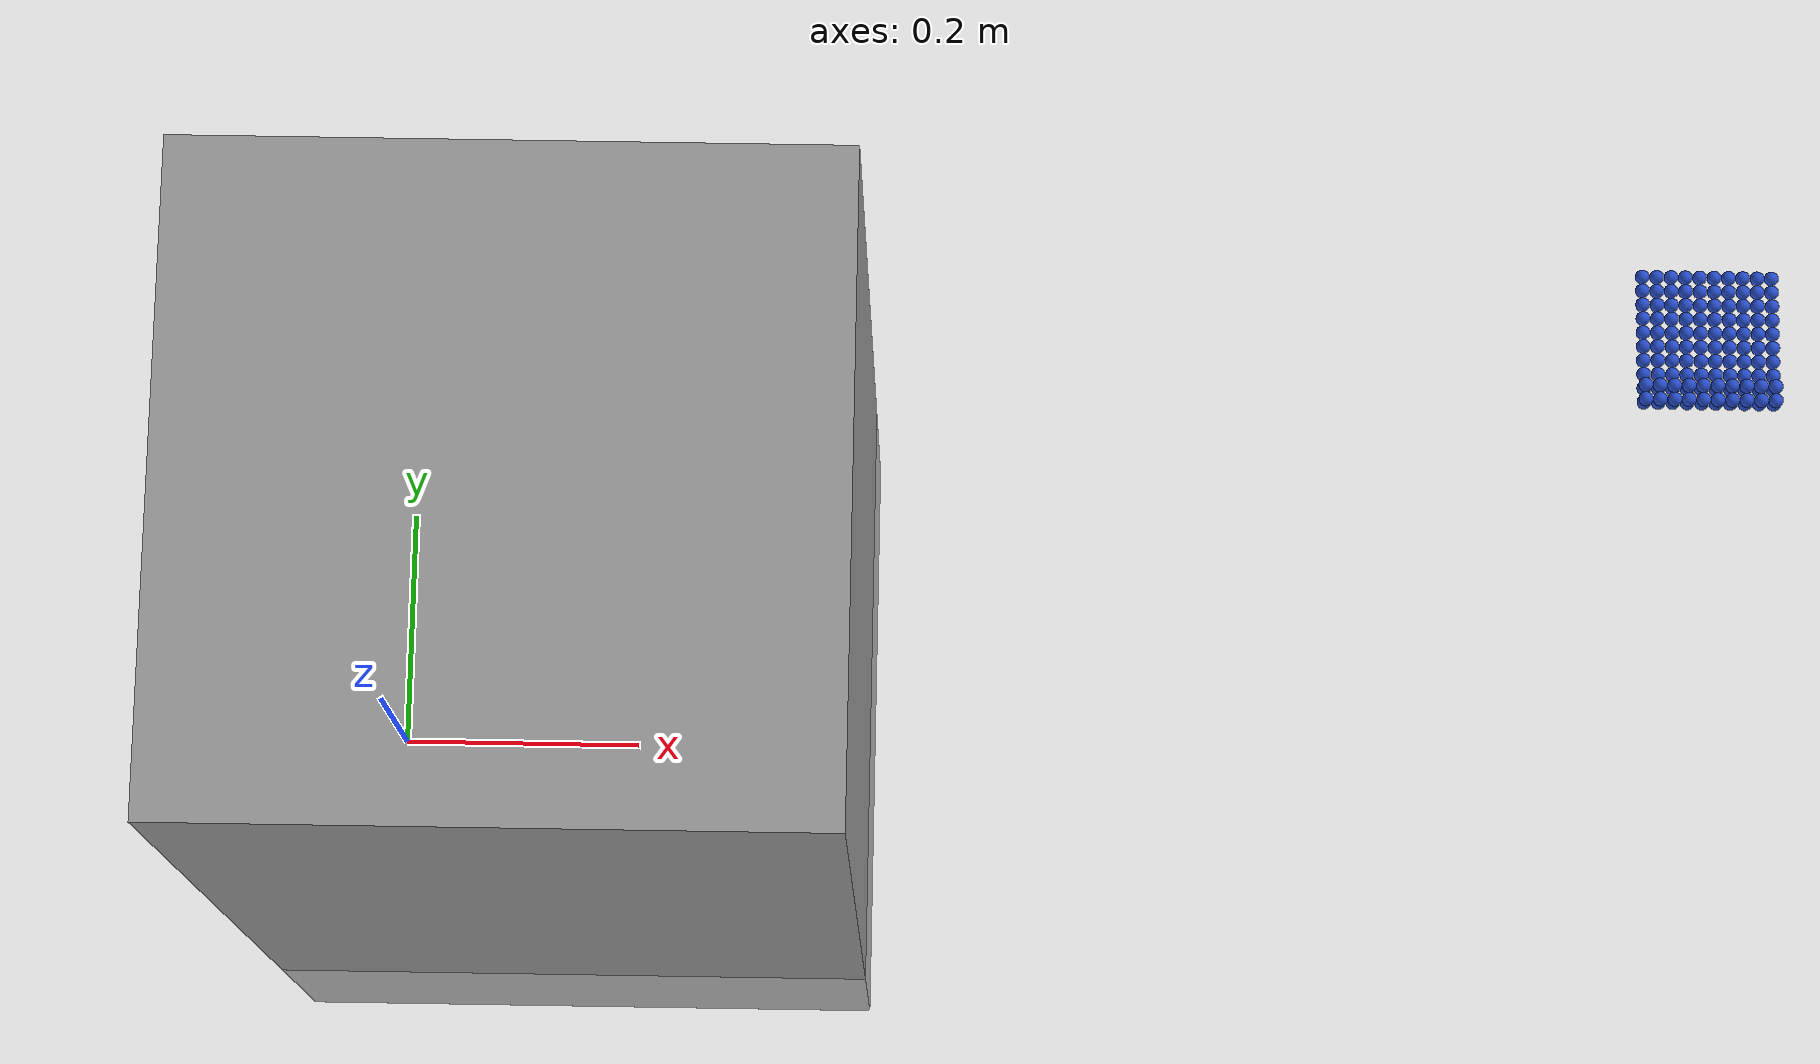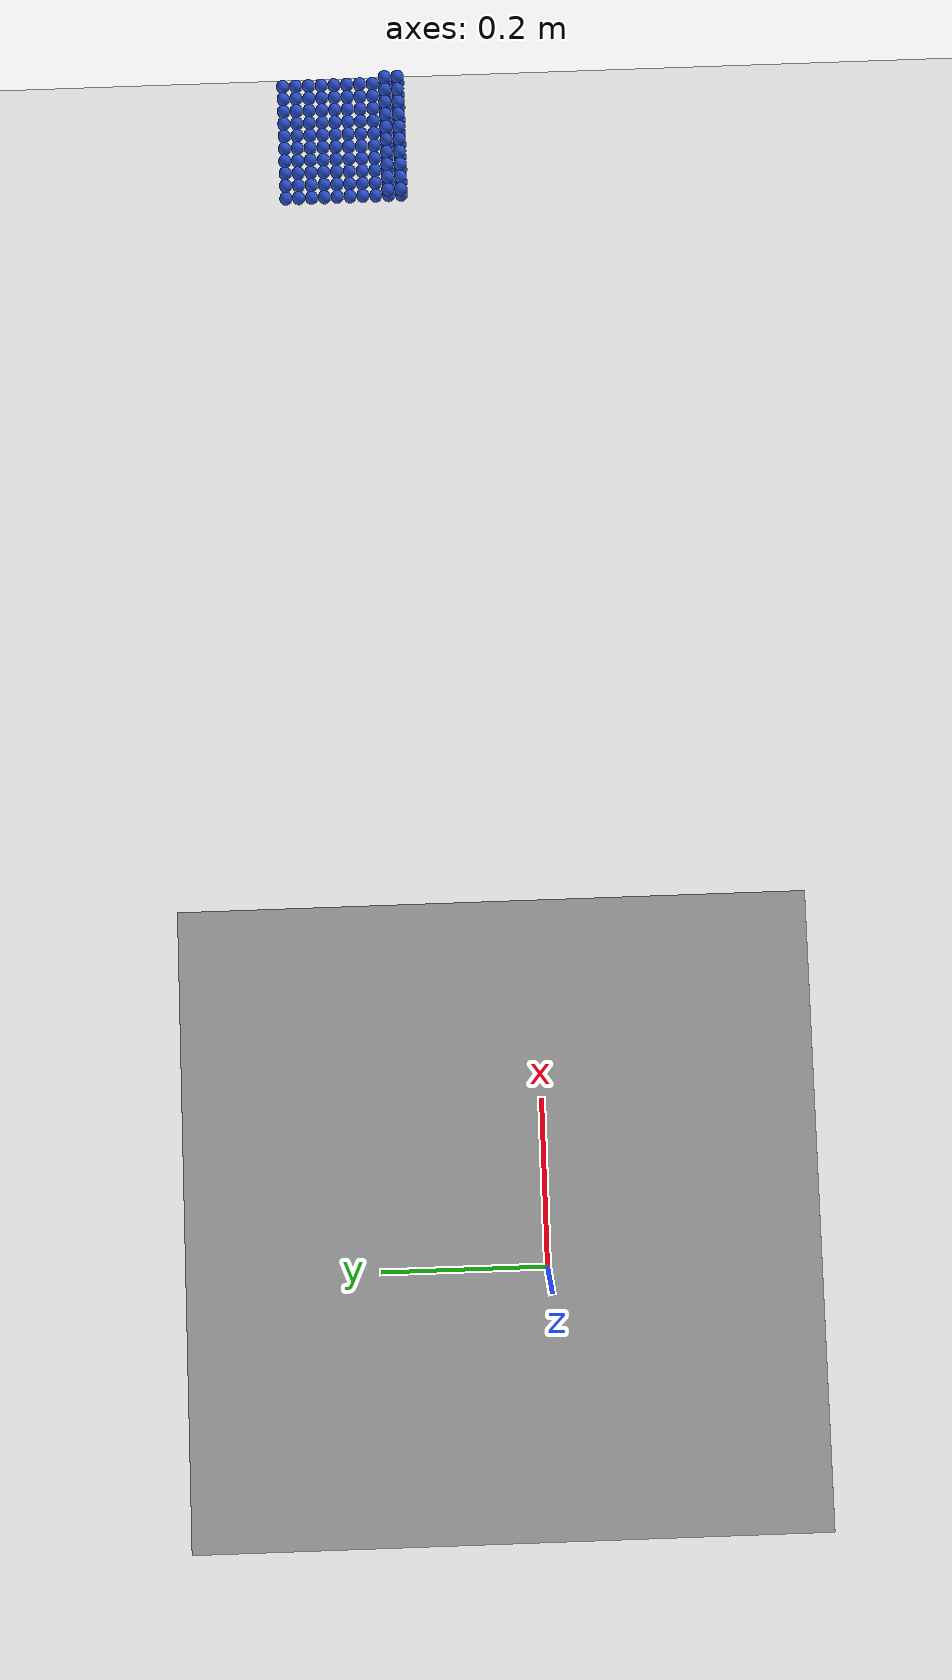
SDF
<sdf version="1.4">
 <world name="default">
  <include><uri>model://ground_plane</uri></include>
  <include><uri>model://sun</uri></include>
  <model name="unit_box_1">
   <pose>0.15 0.05 0.28 0 -0 0</pose>
   <link name="link">
    <inertial>
     <mass>1</mass>
     <inertia><ixx>1</ixx><ixy>0</ixy><ixz>0</ixz><iyy>1</iyy><iyz>0</iyz><izz>1</izz></inertia>
    </inertial>
    <collision name="collision"><geometry><box><size>0.5 0.5 0.55</size></box></geometry></collision>
    <visual name="visual">
     <geometry><box><size>0.5 0.5 1.0</size></box></geometry>
     <material>
      <script><uri>file://media/materials/scripts/gazebo.material</uri><name>Gazebo/Gray</name></script>
     </material>
    </visual>
    <velocity_decay><linear>0</linear><angular>0</angular></velocity_decay>
   </link>
   <static>1</static>
  </model>
  <model name="ball_bearing_0">
   <link name="link">
    <pose>0 0 0.003 0 0 0</pose>
    <inertial>
     <mass>0.0011</mass>
     <inertia>
      <ixx>3.96e-09</ixx>
      <ixy>0</ixy>
      <ixz>0</ixz>
      <iyy>3.96e-09</iyy>
      <iyz>0</iyz>
      <izz>3.96e-09</izz>
     </inertia>
    </inertial>
    <collision name="collision">
     <geometry><sphere><radius>0.005</radius></sphere></geometry>
     <surface><contact><ode><max_vel>0.1</max_vel><min_depth>0.0001</min_depth></ode></contact></surface>
    </collision>
    <visual name="visual">
     <geometry><sphere><radius>0.005</radius></sphere></geometry>
     <material>
      <script><uri>file://media/materials/scripts/gazebo.material</uri><name>Gazebo/Blue</name></script>
     </material>
    </visual>
    <velocity_decay><linear>0</linear><angular>0.005</angular></velocity_decay>
   </link>
   <pose>0.95 0.1 0.85 0.0 0.0 0.0</pose>
  </model>
  <model name="ball_bearing_1">
   <link name="link">
    <pose>0 0 0.003 0 0 0</pose>
    <inertial>
     <mass>0.0011</mass>
     <inertia>
      <ixx>3.96e-09</ixx>
      <ixy>0</ixy>
      <ixz>0</ixz>
      <iyy>3.96e-09</iyy>
      <iyz>0</iyz>
      <izz>3.96e-09</izz>
     </inertia>
    </inertial>
    <collision name="collision">
     <geometry><sphere><radius>0.005</radius></sphere></geometry>
     <surface><contact><ode><max_vel>0.1</max_vel><min_depth>0.0001</min_depth></ode></contact></surface>
    </collision>
    <visual name="visual">
     <geometry><sphere><radius>0.005</radius></sphere></geometry>
     <material>
      <script><uri>file://media/materials/scripts/gazebo.material</uri><name>Gazebo/Blue</name></script>
     </material>
    </visual>
    <velocity_decay><linear>0</linear><angular>0.005</angular></velocity_decay>
   </link>
   <pose>0.96 0.1 0.85 0.0 0.0 0.0</pose>
  </model>
  <model name="ball_bearing_2">
   <link name="link">
    <pose>0 0 0.003 0 0 0</pose>
    <inertial>
     <mass>0.0011</mass>
     <inertia>
      <ixx>3.96e-09</ixx>
      <ixy>0</ixy>
      <ixz>0</ixz>
      <iyy>3.96e-09</iyy>
      <iyz>0</iyz>
      <izz>3.96e-09</izz>
     </inertia>
    </inertial>
    <collision name="collision">
     <geometry><sphere><radius>0.005</radius></sphere></geometry>
     <surface><contact><ode><max_vel>0.1</max_vel><min_depth>0.0001</min_depth></ode></contact></surface>
    </collision>
    <visual name="visual">
     <geometry><sphere><radius>0.005</radius></sphere></geometry>
     <material>
      <script><uri>file://media/materials/scripts/gazebo.material</uri><name>Gazebo/Blue</name></script>
     </material>
    </visual>
    <velocity_decay><linear>0</linear><angular>0.005</angular></velocity_decay>
   </link>
   <pose>0.97 0.1 0.85 0.0 0.0 0.0</pose>
  </model>
  <model name="ball_bearing_3">
   <link name="link">
    <pose>0 0 0.003 0 0 0</pose>
    <inertial>
     <mass>0.0011</mass>
     <inertia>
      <ixx>3.96e-09</ixx>
      <ixy>0</ixy>
      <ixz>0</ixz>
      <iyy>3.96e-09</iyy>
      <iyz>0</iyz>
      <izz>3.96e-09</izz>
     </inertia>
    </inertial>
    <collision name="collision">
     <geometry><sphere><radius>0.005</radius></sphere></geometry>
     <surface><contact><ode><max_vel>0.1</max_vel><min_depth>0.0001</min_depth></ode></contact></surface>
    </collision>
    <visual name="visual">
     <geometry><sphere><radius>0.005</radius></sphere></geometry>
     <material>
      <script><uri>file://media/materials/scripts/gazebo.material</uri><name>Gazebo/Blue</name></script>
     </material>
    </visual>
    <velocity_decay><linear>0</linear><angular>0.005</angular></velocity_decay>
   </link>
   <pose>0.98 0.1 0.85 0.0 0.0 0.0</pose>
  </model>
  <model name="ball_bearing_4">
   <link name="link">
    <pose>0 0 0.003 0 0 0</pose>
    <inertial>
     <mass>0.0011</mass>
     <inertia>
      <ixx>3.96e-09</ixx>
      <ixy>0</ixy>
      <ixz>0</ixz>
      <iyy>3.96e-09</iyy>
      <iyz>0</iyz>
      <izz>3.96e-09</izz>
     </inertia>
    </inertial>
    <collision name="collision">
     <geometry><sphere><radius>0.005</radius></sphere></geometry>
     <surface><contact><ode><max_vel>0.1</max_vel><min_depth>0.0001</min_depth></ode></contact></surface>
    </collision>
    <visual name="visual">
     <geometry><sphere><radius>0.005</radius></sphere></geometry>
     <material>
      <script><uri>file://media/materials/scripts/gazebo.material</uri><name>Gazebo/Blue</name></script>
     </material>
    </visual>
    <velocity_decay><linear>0</linear><angular>0.005</angular></velocity_decay>
   </link>
   <pose>0.99 0.1 0.85 0.0 0.0 0.0</pose>
  </model>
  <model name="ball_bearing_5">
   <link name="link">
    <pose>0 0 0.003 0 0 0</pose>
    <inertial>
     <mass>0.0011</mass>
     <inertia>
      <ixx>3.96e-09</ixx>
      <ixy>0</ixy>
      <ixz>0</ixz>
      <iyy>3.96e-09</iyy>
      <iyz>0</iyz>
      <izz>3.96e-09</izz>
     </inertia>
    </inertial>
    <collision name="collision">
     <geometry><sphere><radius>0.005</radius></sphere></geometry>
     <surface><contact><ode><max_vel>0.1</max_vel><min_depth>0.0001</min_depth></ode></contact></surface>
    </collision>
    <visual name="visual">
     <geometry><sphere><radius>0.005</radius></sphere></geometry>
     <material>
      <script><uri>file://media/materials/scripts/gazebo.material</uri><name>Gazebo/Blue</name></script>
     </material>
    </visual>
    <velocity_decay><linear>0</linear><angular>0.005</angular></velocity_decay>
   </link>
   <pose>1.0 0.1 0.85 0.0 0.0 0.0</pose>
  </model>
  <model name="ball_bearing_6">
   <link name="link">
    <pose>0 0 0.003 0 0 0</pose>
    <inertial>
     <mass>0.0011</mass>
     <inertia>
      <ixx>3.96e-09</ixx>
      <ixy>0</ixy>
      <ixz>0</ixz>
      <iyy>3.96e-09</iyy>
      <iyz>0</iyz>
      <izz>3.96e-09</izz>
     </inertia>
    </inertial>
    <collision name="collision">
     <geometry><sphere><radius>0.005</radius></sphere></geometry>
     <surface><contact><ode><max_vel>0.1</max_vel><min_depth>0.0001</min_depth></ode></contact></surface>
    </collision>
    <visual name="visual">
     <geometry><sphere><radius>0.005</radius></sphere></geometry>
     <material>
      <script><uri>file://media/materials/scripts/gazebo.material</uri><name>Gazebo/Blue</name></script>
     </material>
    </visual>
    <velocity_decay><linear>0</linear><angular>0.005</angular></velocity_decay>
   </link>
   <pose>1.01 0.1 0.85 0.0 0.0 0.0</pose>
  </model>
  <model name="ball_bearing_7">
   <link name="link">
    <pose>0 0 0.003 0 0 0</pose>
    <inertial>
     <mass>0.0011</mass>
     <inertia>
      <ixx>3.96e-09</ixx>
      <ixy>0</ixy>
      <ixz>0</ixz>
      <iyy>3.96e-09</iyy>
      <iyz>0</iyz>
      <izz>3.96e-09</izz>
     </inertia>
    </inertial>
    <collision name="collision">
     <geometry><sphere><radius>0.005</radius></sphere></geometry>
     <surface><contact><ode><max_vel>0.1</max_vel><min_depth>0.0001</min_depth></ode></contact></surface>
    </collision>
    <visual name="visual">
     <geometry><sphere><radius>0.005</radius></sphere></geometry>
     <material>
      <script><uri>file://media/materials/scripts/gazebo.material</uri><name>Gazebo/Blue</name></script>
     </material>
    </visual>
    <velocity_decay><linear>0</linear><angular>0.005</angular></velocity_decay>
   </link>
   <pose>1.02 0.1 0.85 0.0 0.0 0.0</pose>
  </model>
  <model name="ball_bearing_8">
   <link name="link">
    <pose>0 0 0.003 0 0 0</pose>
    <inertial>
     <mass>0.0011</mass>
     <inertia>
      <ixx>3.96e-09</ixx>
      <ixy>0</ixy>
      <ixz>0</ixz>
      <iyy>3.96e-09</iyy>
      <iyz>0</iyz>
      <izz>3.96e-09</izz>
     </inertia>
    </inertial>
    <collision name="collision">
     <geometry><sphere><radius>0.005</radius></sphere></geometry>
     <surface><contact><ode><max_vel>0.1</max_vel><min_depth>0.0001</min_depth></ode></contact></surface>
    </collision>
    <visual name="visual">
     <geometry><sphere><radius>0.005</radius></sphere></geometry>
     <material>
      <script><uri>file://media/materials/scripts/gazebo.material</uri><name>Gazebo/Blue</name></script>
     </material>
    </visual>
    <velocity_decay><linear>0</linear><angular>0.005</angular></velocity_decay>
   </link>
   <pose>1.03 0.1 0.85 0.0 0.0 0.0</pose>
  </model>
  <model name="ball_bearing_9">
   <link name="link">
    <pose>0 0 0.003 0 0 0</pose>
    <inertial>
     <mass>0.0011</mass>
     <inertia>
      <ixx>3.96e-09</ixx>
      <ixy>0</ixy>
      <ixz>0</ixz>
      <iyy>3.96e-09</iyy>
      <iyz>0</iyz>
      <izz>3.96e-09</izz>
     </inertia>
    </inertial>
    <collision name="collision">
     <geometry><sphere><radius>0.005</radius></sphere></geometry>
     <surface><contact><ode><max_vel>0.1</max_vel><min_depth>0.0001</min_depth></ode></contact></surface>
    </collision>
    <visual name="visual">
     <geometry><sphere><radius>0.005</radius></sphere></geometry>
     <material>
      <script><uri>file://media/materials/scripts/gazebo.material</uri><name>Gazebo/Blue</name></script>
     </material>
    </visual>
    <velocity_decay><linear>0</linear><angular>0.005</angular></velocity_decay>
   </link>
   <pose>1.04 0.1 0.85 0.0 0.0 0.0</pose>
  </model>
  <model name="ball_bearing_10">
   <link name="link">
    <pose>0 0 0.003 0 0 0</pose>
    <inertial>
     <mass>0.0011</mass>
     <inertia>
      <ixx>3.96e-09</ixx>
      <ixy>0</ixy>
      <ixz>0</ixz>
      <iyy>3.96e-09</iyy>
      <iyz>0</iyz>
      <izz>3.96e-09</izz>
     </inertia>
    </inertial>
    <collision name="collision">
     <geometry><sphere><radius>0.005</radius></sphere></geometry>
     <surface><contact><ode><max_vel>0.1</max_vel><min_depth>0.0001</min_depth></ode></contact></surface>
    </collision>
    <visual name="visual">
     <geometry><sphere><radius>0.005</radius></sphere></geometry>
     <material>
      <script><uri>file://media/materials/scripts/gazebo.material</uri><name>Gazebo/Blue</name></script>
     </material>
    </visual>
    <velocity_decay><linear>0</linear><angular>0.005</angular></velocity_decay>
   </link>
   <pose>0.95 0.11 0.85 0.0 0.0 0.0</pose>
  </model>
  <model name="ball_bearing_11">
   <link name="link">
    <pose>0 0 0.003 0 0 0</pose>
    <inertial>
     <mass>0.0011</mass>
     <inertia>
      <ixx>3.96e-09</ixx>
      <ixy>0</ixy>
      <ixz>0</ixz>
      <iyy>3.96e-09</iyy>
      <iyz>0</iyz>
      <izz>3.96e-09</izz>
     </inertia>
    </inertial>
    <collision name="collision">
     <geometry><sphere><radius>0.005</radius></sphere></geometry>
     <surface><contact><ode><max_vel>0.1</max_vel><min_depth>0.0001</min_depth></ode></contact></surface>
    </collision>
    <visual name="visual">
     <geometry><sphere><radius>0.005</radius></sphere></geometry>
     <material>
      <script><uri>file://media/materials/scripts/gazebo.material</uri><name>Gazebo/Blue</name></script>
     </material>
    </visual>
    <velocity_decay><linear>0</linear><angular>0.005</angular></velocity_decay>
   </link>
   <pose>0.96 0.11 0.85 0.0 0.0 0.0</pose>
  </model>
  <model name="ball_bearing_12">
   <link name="link">
    <pose>0 0 0.003 0 0 0</pose>
    <inertial>
     <mass>0.0011</mass>
     <inertia>
      <ixx>3.96e-09</ixx>
      <ixy>0</ixy>
      <ixz>0</ixz>
      <iyy>3.96e-09</iyy>
      <iyz>0</iyz>
      <izz>3.96e-09</izz>
     </inertia>
    </inertial>
    <collision name="collision">
     <geometry><sphere><radius>0.005</radius></sphere></geometry>
     <surface><contact><ode><max_vel>0.1</max_vel><min_depth>0.0001</min_depth></ode></contact></surface>
    </collision>
    <visual name="visual">
     <geometry><sphere><radius>0.005</radius></sphere></geometry>
     <material>
      <script><uri>file://media/materials/scripts/gazebo.material</uri><name>Gazebo/Blue</name></script>
     </material>
    </visual>
    <velocity_decay><linear>0</linear><angular>0.005</angular></velocity_decay>
   </link>
   <pose>0.97 0.11 0.85 0.0 0.0 0.0</pose>
  </model>
  <model name="ball_bearing_13">
   <link name="link">
    <pose>0 0 0.003 0 0 0</pose>
    <inertial>
     <mass>0.0011</mass>
     <inertia>
      <ixx>3.96e-09</ixx>
      <ixy>0</ixy>
      <ixz>0</ixz>
      <iyy>3.96e-09</iyy>
      <iyz>0</iyz>
      <izz>3.96e-09</izz>
     </inertia>
    </inertial>
    <collision name="collision">
     <geometry><sphere><radius>0.005</radius></sphere></geometry>
     <surface><contact><ode><max_vel>0.1</max_vel><min_depth>0.0001</min_depth></ode></contact></surface>
    </collision>
    <visual name="visual">
     <geometry><sphere><radius>0.005</radius></sphere></geometry>
     <material>
      <script><uri>file://media/materials/scripts/gazebo.material</uri><name>Gazebo/Blue</name></script>
     </material>
    </visual>
    <velocity_decay><linear>0</linear><angular>0.005</angular></velocity_decay>
   </link>
   <pose>0.98 0.11 0.85 0.0 0.0 0.0</pose>
  </model>
  <model name="ball_bearing_14">
   <link name="link">
    <pose>0 0 0.003 0 0 0</pose>
    <inertial>
     <mass>0.0011</mass>
     <inertia>
      <ixx>3.96e-09</ixx>
      <ixy>0</ixy>
      <ixz>0</ixz>
      <iyy>3.96e-09</iyy>
      <iyz>0</iyz>
      <izz>3.96e-09</izz>
     </inertia>
    </inertial>
    <collision name="collision">
     <geometry><sphere><radius>0.005</radius></sphere></geometry>
     <surface><contact><ode><max_vel>0.1</max_vel><min_depth>0.0001</min_depth></ode></contact></surface>
    </collision>
    <visual name="visual">
     <geometry><sphere><radius>0.005</radius></sphere></geometry>
     <material>
      <script><uri>file://media/materials/scripts/gazebo.material</uri><name>Gazebo/Blue</name></script>
     </material>
    </visual>
    <velocity_decay><linear>0</linear><angular>0.005</angular></velocity_decay>
   </link>
   <pose>0.99 0.11 0.85 0.0 0.0 0.0</pose>
  </model>
  <model name="ball_bearing_15">
   <link name="link">
    <pose>0 0 0.003 0 0 0</pose>
    <inertial>
     <mass>0.0011</mass>
     <inertia>
      <ixx>3.96e-09</ixx>
      <ixy>0</ixy>
      <ixz>0</ixz>
      <iyy>3.96e-09</iyy>
      <iyz>0</iyz>
      <izz>3.96e-09</izz>
     </inertia>
    </inertial>
    <collision name="collision">
     <geometry><sphere><radius>0.005</radius></sphere></geometry>
     <surface><contact><ode><max_vel>0.1</max_vel><min_depth>0.0001</min_depth></ode></contact></surface>
    </collision>
    <visual name="visual">
     <geometry><sphere><radius>0.005</radius></sphere></geometry>
     <material>
      <script><uri>file://media/materials/scripts/gazebo.material</uri><name>Gazebo/Blue</name></script>
     </material>
    </visual>
    <velocity_decay><linear>0</linear><angular>0.005</angular></velocity_decay>
   </link>
   <pose>1.0 0.11 0.85 0.0 0.0 0.0</pose>
  </model>
  <model name="ball_bearing_16">
   <link name="link">
    <pose>0 0 0.003 0 0 0</pose>
    <inertial>
     <mass>0.0011</mass>
     <inertia>
      <ixx>3.96e-09</ixx>
      <ixy>0</ixy>
      <ixz>0</ixz>
      <iyy>3.96e-09</iyy>
      <iyz>0</iyz>
      <izz>3.96e-09</izz>
     </inertia>
    </inertial>
    <collision name="collision">
     <geometry><sphere><radius>0.005</radius></sphere></geometry>
     <surface><contact><ode><max_vel>0.1</max_vel><min_depth>0.0001</min_depth></ode></contact></surface>
    </collision>
    <visual name="visual">
     <geometry><sphere><radius>0.005</radius></sphere></geometry>
     <material>
      <script><uri>file://media/materials/scripts/gazebo.material</uri><name>Gazebo/Blue</name></script>
     </material>
    </visual>
    <velocity_decay><linear>0</linear><angular>0.005</angular></velocity_decay>
   </link>
   <pose>1.01 0.11 0.85 0.0 0.0 0.0</pose>
  </model>
  <model name="ball_bearing_17">
   <link name="link">
    <pose>0 0 0.003 0 0 0</pose>
    <inertial>
     <mass>0.0011</mass>
     <inertia>
      <ixx>3.96e-09</ixx>
      <ixy>0</ixy>
      <ixz>0</ixz>
      <iyy>3.96e-09</iyy>
      <iyz>0</iyz>
      <izz>3.96e-09</izz>
     </inertia>
    </inertial>
    <collision name="collision">
     <geometry><sphere><radius>0.005</radius></sphere></geometry>
     <surface><contact><ode><max_vel>0.1</max_vel><min_depth>0.0001</min_depth></ode></contact></surface>
    </collision>
    <visual name="visual">
     <geometry><sphere><radius>0.005</radius></sphere></geometry>
     <material>
      <script><uri>file://media/materials/scripts/gazebo.material</uri><name>Gazebo/Blue</name></script>
     </material>
    </visual>
    <velocity_decay><linear>0</linear><angular>0.005</angular></velocity_decay>
   </link>
   <pose>1.02 0.11 0.85 0.0 0.0 0.0</pose>
  </model>
  <model name="ball_bearing_18">
   <link name="link">
    <pose>0 0 0.003 0 0 0</pose>
    <inertial>
     <mass>0.0011</mass>
     <inertia>
      <ixx>3.96e-09</ixx>
      <ixy>0</ixy>
      <ixz>0</ixz>
      <iyy>3.96e-09</iyy>
      <iyz>0</iyz>
      <izz>3.96e-09</izz>
     </inertia>
    </inertial>
    <collision name="collision">
     <geometry><sphere><radius>0.005</radius></sphere></geometry>
     <surface><contact><ode><max_vel>0.1</max_vel><min_depth>0.0001</min_depth></ode></contact></surface>
    </collision>
    <visual name="visual">
     <geometry><sphere><radius>0.005</radius></sphere></geometry>
     <material>
      <script><uri>file://media/materials/scripts/gazebo.material</uri><name>Gazebo/Blue</name></script>
     </material>
    </visual>
    <velocity_decay><linear>0</linear><angular>0.005</angular></velocity_decay>
   </link>
   <pose>1.03 0.11 0.85 0.0 0.0 0.0</pose>
  </model>
  <model name="ball_bearing_19">
   <link name="link">
    <pose>0 0 0.003 0 0 0</pose>
    <inertial>
     <mass>0.0011</mass>
     <inertia>
      <ixx>3.96e-09</ixx>
      <ixy>0</ixy>
      <ixz>0</ixz>
      <iyy>3.96e-09</iyy>
      <iyz>0</iyz>
      <izz>3.96e-09</izz>
     </inertia>
    </inertial>
    <collision name="collision">
     <geometry><sphere><radius>0.005</radius></sphere></geometry>
     <surface><contact><ode><max_vel>0.1</max_vel><min_depth>0.0001</min_depth></ode></contact></surface>
    </collision>
    <visual name="visual">
     <geometry><sphere><radius>0.005</radius></sphere></geometry>
     <material>
      <script><uri>file://media/materials/scripts/gazebo.material</uri><name>Gazebo/Blue</name></script>
     </material>
    </visual>
    <velocity_decay><linear>0</linear><angular>0.005</angular></velocity_decay>
   </link>
   <pose>1.04 0.11 0.85 0.0 0.0 0.0</pose>
  </model>
  <model name="ball_bearing_20">
   <link name="link">
    <pose>0 0 0.003 0 0 0</pose>
    <inertial>
     <mass>0.0011</mass>
     <inertia>
      <ixx>3.96e-09</ixx>
      <ixy>0</ixy>
      <ixz>0</ixz>
      <iyy>3.96e-09</iyy>
      <iyz>0</iyz>
      <izz>3.96e-09</izz>
     </inertia>
    </inertial>
    <collision name="collision">
     <geometry><sphere><radius>0.005</radius></sphere></geometry>
     <surface><contact><ode><max_vel>0.1</max_vel><min_depth>0.0001</min_depth></ode></contact></surface>
    </collision>
    <visual name="visual">
     <geometry><sphere><radius>0.005</radius></sphere></geometry>
     <material>
      <script><uri>file://media/materials/scripts/gazebo.material</uri><name>Gazebo/Blue</name></script>
     </material>
    </visual>
    <velocity_decay><linear>0</linear><angular>0.005</angular></velocity_decay>
   </link>
   <pose>0.95 0.12 0.85 0.0 0.0 0.0</pose>
  </model>
  <model name="ball_bearing_21">
   <link name="link">
    <pose>0 0 0.003 0 0 0</pose>
    <inertial>
     <mass>0.0011</mass>
     <inertia>
      <ixx>3.96e-09</ixx>
      <ixy>0</ixy>
      <ixz>0</ixz>
      <iyy>3.96e-09</iyy>
      <iyz>0</iyz>
      <izz>3.96e-09</izz>
     </inertia>
    </inertial>
    <collision name="collision">
     <geometry><sphere><radius>0.005</radius></sphere></geometry>
     <surface><contact><ode><max_vel>0.1</max_vel><min_depth>0.0001</min_depth></ode></contact></surface>
    </collision>
    <visual name="visual">
     <geometry><sphere><radius>0.005</radius></sphere></geometry>
     <material>
      <script><uri>file://media/materials/scripts/gazebo.material</uri><name>Gazebo/Blue</name></script>
     </material>
    </visual>
    <velocity_decay><linear>0</linear><angular>0.005</angular></velocity_decay>
   </link>
   <pose>0.96 0.12 0.85 0.0 0.0 0.0</pose>
  </model>
  <model name="ball_bearing_22">
   <link name="link">
    <pose>0 0 0.003 0 0 0</pose>
    <inertial>
     <mass>0.0011</mass>
     <inertia>
      <ixx>3.96e-09</ixx>
      <ixy>0</ixy>
      <ixz>0</ixz>
      <iyy>3.96e-09</iyy>
      <iyz>0</iyz>
      <izz>3.96e-09</izz>
     </inertia>
    </inertial>
    <collision name="collision">
     <geometry><sphere><radius>0.005</radius></sphere></geometry>
     <surface><contact><ode><max_vel>0.1</max_vel><min_depth>0.0001</min_depth></ode></contact></surface>
    </collision>
    <visual name="visual">
     <geometry><sphere><radius>0.005</radius></sphere></geometry>
     <material>
      <script><uri>file://media/materials/scripts/gazebo.material</uri><name>Gazebo/Blue</name></script>
     </material>
    </visual>
    <velocity_decay><linear>0</linear><angular>0.005</angular></velocity_decay>
   </link>
   <pose>0.97 0.12 0.85 0.0 0.0 0.0</pose>
  </model>
  <model name="ball_bearing_23">
   <link name="link">
    <pose>0 0 0.003 0 0 0</pose>
    <inertial>
     <mass>0.0011</mass>
     <inertia>
      <ixx>3.96e-09</ixx>
      <ixy>0</ixy>
      <ixz>0</ixz>
      <iyy>3.96e-09</iyy>
      <iyz>0</iyz>
      <izz>3.96e-09</izz>
     </inertia>
    </inertial>
    <collision name="collision">
     <geometry><sphere><radius>0.005</radius></sphere></geometry>
     <surface><contact><ode><max_vel>0.1</max_vel><min_depth>0.0001</min_depth></ode></contact></surface>
    </collision>
    <visual name="visual">
     <geometry><sphere><radius>0.005</radius></sphere></geometry>
     <material>
      <script><uri>file://media/materials/scripts/gazebo.material</uri><name>Gazebo/Blue</name></script>
     </material>
    </visual>
    <velocity_decay><linear>0</linear><angular>0.005</angular></velocity_decay>
   </link>
   <pose>0.98 0.12 0.85 0.0 0.0 0.0</pose>
  </model>
  <model name="ball_bearing_24">
   <link name="link">
    <pose>0 0 0.003 0 0 0</pose>
    <inertial>
     <mass>0.0011</mass>
     <inertia>
      <ixx>3.96e-09</ixx>
      <ixy>0</ixy>
      <ixz>0</ixz>
      <iyy>3.96e-09</iyy>
      <iyz>0</iyz>
      <izz>3.96e-09</izz>
     </inertia>
    </inertial>
    <collision name="collision">
     <geometry><sphere><radius>0.005</radius></sphere></geometry>
     <surface><contact><ode><max_vel>0.1</max_vel><min_depth>0.0001</min_depth></ode></contact></surface>
    </collision>
    <visual name="visual">
     <geometry><sphere><radius>0.005</radius></sphere></geometry>
     <material>
      <script><uri>file://media/materials/scripts/gazebo.material</uri><name>Gazebo/Blue</name></script>
     </material>
    </visual>
    <velocity_decay><linear>0</linear><angular>0.005</angular></velocity_decay>
   </link>
   <pose>0.99 0.12 0.85 0.0 0.0 0.0</pose>
  </model>
  <model name="ball_bearing_25">
   <link name="link">
    <pose>0 0 0.003 0 0 0</pose>
    <inertial>
     <mass>0.0011</mass>
     <inertia>
      <ixx>3.96e-09</ixx>
      <ixy>0</ixy>
      <ixz>0</ixz>
      <iyy>3.96e-09</iyy>
      <iyz>0</iyz>
      <izz>3.96e-09</izz>
     </inertia>
    </inertial>
    <collision name="collision">
     <geometry><sphere><radius>0.005</radius></sphere></geometry>
     <surface><contact><ode><max_vel>0.1</max_vel><min_depth>0.0001</min_depth></ode></contact></surface>
    </collision>
    <visual name="visual">
     <geometry><sphere><radius>0.005</radius></sphere></geometry>
     <material>
      <script><uri>file://media/materials/scripts/gazebo.material</uri><name>Gazebo/Blue</name></script>
     </material>
    </visual>
    <velocity_decay><linear>0</linear><angular>0.005</angular></velocity_decay>
   </link>
   <pose>1.0 0.12 0.85 0.0 0.0 0.0</pose>
  </model>
  <model name="ball_bearing_26">
   <link name="link">
    <pose>0 0 0.003 0 0 0</pose>
    <inertial>
     <mass>0.0011</mass>
     <inertia>
      <ixx>3.96e-09</ixx>
      <ixy>0</ixy>
      <ixz>0</ixz>
      <iyy>3.96e-09</iyy>
      <iyz>0</iyz>
      <izz>3.96e-09</izz>
     </inertia>
    </inertial>
    <collision name="collision">
     <geometry><sphere><radius>0.005</radius></sphere></geometry>
     <surface><contact><ode><max_vel>0.1</max_vel><min_depth>0.0001</min_depth></ode></contact></surface>
    </collision>
    <visual name="visual">
     <geometry><sphere><radius>0.005</radius></sphere></geometry>
     <material>
      <script><uri>file://media/materials/scripts/gazebo.material</uri><name>Gazebo/Blue</name></script>
     </material>
    </visual>
    <velocity_decay><linear>0</linear><angular>0.005</angular></velocity_decay>
   </link>
   <pose>1.01 0.12 0.85 0.0 0.0 0.0</pose>
  </model>
  <model name="ball_bearing_27">
   <link name="link">
    <pose>0 0 0.003 0 0 0</pose>
    <inertial>
     <mass>0.0011</mass>
     <inertia>
      <ixx>3.96e-09</ixx>
      <ixy>0</ixy>
      <ixz>0</ixz>
      <iyy>3.96e-09</iyy>
      <iyz>0</iyz>
      <izz>3.96e-09</izz>
     </inertia>
    </inertial>
    <collision name="collision">
     <geometry><sphere><radius>0.005</radius></sphere></geometry>
     <surface><contact><ode><max_vel>0.1</max_vel><min_depth>0.0001</min_depth></ode></contact></surface>
    </collision>
    <visual name="visual">
     <geometry><sphere><radius>0.005</radius></sphere></geometry>
     <material>
      <script><uri>file://media/materials/scripts/gazebo.material</uri><name>Gazebo/Blue</name></script>
     </material>
    </visual>
    <velocity_decay><linear>0</linear><angular>0.005</angular></velocity_decay>
   </link>
   <pose>1.02 0.12 0.85 0.0 0.0 0.0</pose>
  </model>
  <model name="ball_bearing_28">
   <link name="link">
    <pose>0 0 0.003 0 0 0</pose>
    <inertial>
     <mass>0.0011</mass>
     <inertia>
      <ixx>3.96e-09</ixx>
      <ixy>0</ixy>
      <ixz>0</ixz>
      <iyy>3.96e-09</iyy>
      <iyz>0</iyz>
      <izz>3.96e-09</izz>
     </inertia>
    </inertial>
    <collision name="collision">
     <geometry><sphere><radius>0.005</radius></sphere></geometry>
     <surface><contact><ode><max_vel>0.1</max_vel><min_depth>0.0001</min_depth></ode></contact></surface>
    </collision>
    <visual name="visual">
     <geometry><sphere><radius>0.005</radius></sphere></geometry>
     <material>
      <script><uri>file://media/materials/scripts/gazebo.material</uri><name>Gazebo/Blue</name></script>
     </material>
    </visual>
    <velocity_decay><linear>0</linear><angular>0.005</angular></velocity_decay>
   </link>
   <pose>1.03 0.12 0.85 0.0 0.0 0.0</pose>
  </model>
  <model name="ball_bearing_29">
   <link name="link">
    <pose>0 0 0.003 0 0 0</pose>
    <inertial>
     <mass>0.0011</mass>
     <inertia>
      <ixx>3.96e-09</ixx>
      <ixy>0</ixy>
      <ixz>0</ixz>
      <iyy>3.96e-09</iyy>
      <iyz>0</iyz>
      <izz>3.96e-09</izz>
     </inertia>
    </inertial>
    <collision name="collision">
     <geometry><sphere><radius>0.005</radius></sphere></geometry>
     <surface><contact><ode><max_vel>0.1</max_vel><min_depth>0.0001</min_depth></ode></contact></surface>
    </collision>
    <visual name="visual">
     <geometry><sphere><radius>0.005</radius></sphere></geometry>
     <material>
      <script><uri>file://media/materials/scripts/gazebo.material</uri><name>Gazebo/Blue</name></script>
     </material>
    </visual>
    <velocity_decay><linear>0</linear><angular>0.005</angular></velocity_decay>
   </link>
   <pose>1.04 0.12 0.85 0.0 0.0 0.0</pose>
  </model>
  <model name="ball_bearing_30">
   <link name="link">
    <pose>0 0 0.003 0 0 0</pose>
    <inertial>
     <mass>0.0011</mass>
     <inertia>
      <ixx>3.96e-09</ixx>
      <ixy>0</ixy>
      <ixz>0</ixz>
      <iyy>3.96e-09</iyy>
      <iyz>0</iyz>
      <izz>3.96e-09</izz>
     </inertia>
    </inertial>
    <collision name="collision">
     <geometry><sphere><radius>0.005</radius></sphere></geometry>
     <surface><contact><ode><max_vel>0.1</max_vel><min_depth>0.0001</min_depth></ode></contact></surface>
    </collision>
    <visual name="visual">
     <geometry><sphere><radius>0.005</radius></sphere></geometry>
     <material>
      <script><uri>file://media/materials/scripts/gazebo.material</uri><name>Gazebo/Blue</name></script>
     </material>
    </visual>
    <velocity_decay><linear>0</linear><angular>0.005</angular></velocity_decay>
   </link>
   <pose>0.95 0.13 0.85 0.0 0.0 0.0</pose>
  </model>
  <model name="ball_bearing_31">
   <link name="link">
    <pose>0 0 0.003 0 0 0</pose>
    <inertial>
     <mass>0.0011</mass>
     <inertia>
      <ixx>3.96e-09</ixx>
      <ixy>0</ixy>
      <ixz>0</ixz>
      <iyy>3.96e-09</iyy>
      <iyz>0</iyz>
      <izz>3.96e-09</izz>
     </inertia>
    </inertial>
    <collision name="collision">
     <geometry><sphere><radius>0.005</radius></sphere></geometry>
     <surface><contact><ode><max_vel>0.1</max_vel><min_depth>0.0001</min_depth></ode></contact></surface>
    </collision>
    <visual name="visual">
     <geometry><sphere><radius>0.005</radius></sphere></geometry>
     <material>
      <script><uri>file://media/materials/scripts/gazebo.material</uri><name>Gazebo/Blue</name></script>
     </material>
    </visual>
    <velocity_decay><linear>0</linear><angular>0.005</angular></velocity_decay>
   </link>
   <pose>0.96 0.13 0.85 0.0 0.0 0.0</pose>
  </model>
  <model name="ball_bearing_32">
   <link name="link">
    <pose>0 0 0.003 0 0 0</pose>
    <inertial>
     <mass>0.0011</mass>
     <inertia>
      <ixx>3.96e-09</ixx>
      <ixy>0</ixy>
      <ixz>0</ixz>
      <iyy>3.96e-09</iyy>
      <iyz>0</iyz>
      <izz>3.96e-09</izz>
     </inertia>
    </inertial>
    <collision name="collision">
     <geometry><sphere><radius>0.005</radius></sphere></geometry>
     <surface><contact><ode><max_vel>0.1</max_vel><min_depth>0.0001</min_depth></ode></contact></surface>
    </collision>
    <visual name="visual">
     <geometry><sphere><radius>0.005</radius></sphere></geometry>
     <material>
      <script><uri>file://media/materials/scripts/gazebo.material</uri><name>Gazebo/Blue</name></script>
     </material>
    </visual>
    <velocity_decay><linear>0</linear><angular>0.005</angular></velocity_decay>
   </link>
   <pose>0.97 0.13 0.85 0.0 0.0 0.0</pose>
  </model>
  <model name="ball_bearing_33">
   <link name="link">
    <pose>0 0 0.003 0 0 0</pose>
    <inertial>
     <mass>0.0011</mass>
     <inertia>
      <ixx>3.96e-09</ixx>
      <ixy>0</ixy>
      <ixz>0</ixz>
      <iyy>3.96e-09</iyy>
      <iyz>0</iyz>
      <izz>3.96e-09</izz>
     </inertia>
    </inertial>
    <collision name="collision">
     <geometry><sphere><radius>0.005</radius></sphere></geometry>
     <surface><contact><ode><max_vel>0.1</max_vel><min_depth>0.0001</min_depth></ode></contact></surface>
    </collision>
    <visual name="visual">
     <geometry><sphere><radius>0.005</radius></sphere></geometry>
     <material>
      <script><uri>file://media/materials/scripts/gazebo.material</uri><name>Gazebo/Blue</name></script>
     </material>
    </visual>
    <velocity_decay><linear>0</linear><angular>0.005</angular></velocity_decay>
   </link>
   <pose>0.98 0.13 0.85 0.0 0.0 0.0</pose>
  </model>
  <model name="ball_bearing_34">
   <link name="link">
    <pose>0 0 0.003 0 0 0</pose>
    <inertial>
     <mass>0.0011</mass>
     <inertia>
      <ixx>3.96e-09</ixx>
      <ixy>0</ixy>
      <ixz>0</ixz>
      <iyy>3.96e-09</iyy>
      <iyz>0</iyz>
      <izz>3.96e-09</izz>
     </inertia>
    </inertial>
    <collision name="collision">
     <geometry><sphere><radius>0.005</radius></sphere></geometry>
     <surface><contact><ode><max_vel>0.1</max_vel><min_depth>0.0001</min_depth></ode></contact></surface>
    </collision>
    <visual name="visual">
     <geometry><sphere><radius>0.005</radius></sphere></geometry>
     <material>
      <script><uri>file://media/materials/scripts/gazebo.material</uri><name>Gazebo/Blue</name></script>
     </material>
    </visual>
    <velocity_decay><linear>0</linear><angular>0.005</angular></velocity_decay>
   </link>
   <pose>0.99 0.13 0.85 0.0 0.0 0.0</pose>
  </model>
  <model name="ball_bearing_35">
   <link name="link">
    <pose>0 0 0.003 0 0 0</pose>
    <inertial>
     <mass>0.0011</mass>
     <inertia>
      <ixx>3.96e-09</ixx>
      <ixy>0</ixy>
      <ixz>0</ixz>
      <iyy>3.96e-09</iyy>
      <iyz>0</iyz>
      <izz>3.96e-09</izz>
     </inertia>
    </inertial>
    <collision name="collision">
     <geometry><sphere><radius>0.005</radius></sphere></geometry>
     <surface><contact><ode><max_vel>0.1</max_vel><min_depth>0.0001</min_depth></ode></contact></surface>
    </collision>
    <visual name="visual">
     <geometry><sphere><radius>0.005</radius></sphere></geometry>
     <material>
      <script><uri>file://media/materials/scripts/gazebo.material</uri><name>Gazebo/Blue</name></script>
     </material>
    </visual>
    <velocity_decay><linear>0</linear><angular>0.005</angular></velocity_decay>
   </link>
   <pose>1.0 0.13 0.85 0.0 0.0 0.0</pose>
  </model>
  <model name="ball_bearing_36">
   <link name="link">
    <pose>0 0 0.003 0 0 0</pose>
    <inertial>
     <mass>0.0011</mass>
     <inertia>
      <ixx>3.96e-09</ixx>
      <ixy>0</ixy>
      <ixz>0</ixz>
      <iyy>3.96e-09</iyy>
      <iyz>0</iyz>
      <izz>3.96e-09</izz>
     </inertia>
    </inertial>
    <collision name="collision">
     <geometry><sphere><radius>0.005</radius></sphere></geometry>
     <surface><contact><ode><max_vel>0.1</max_vel><min_depth>0.0001</min_depth></ode></contact></surface>
    </collision>
    <visual name="visual">
     <geometry><sphere><radius>0.005</radius></sphere></geometry>
     <material>
      <script><uri>file://media/materials/scripts/gazebo.material</uri><name>Gazebo/Blue</name></script>
     </material>
    </visual>
    <velocity_decay><linear>0</linear><angular>0.005</angular></velocity_decay>
   </link>
   <pose>1.01 0.13 0.85 0.0 0.0 0.0</pose>
  </model>
  <model name="ball_bearing_37">
   <link name="link">
    <pose>0 0 0.003 0 0 0</pose>
    <inertial>
     <mass>0.0011</mass>
     <inertia>
      <ixx>3.96e-09</ixx>
      <ixy>0</ixy>
      <ixz>0</ixz>
      <iyy>3.96e-09</iyy>
      <iyz>0</iyz>
      <izz>3.96e-09</izz>
     </inertia>
    </inertial>
    <collision name="collision">
     <geometry><sphere><radius>0.005</radius></sphere></geometry>
     <surface><contact><ode><max_vel>0.1</max_vel><min_depth>0.0001</min_depth></ode></contact></surface>
    </collision>
    <visual name="visual">
     <geometry><sphere><radius>0.005</radius></sphere></geometry>
     <material>
      <script><uri>file://media/materials/scripts/gazebo.material</uri><name>Gazebo/Blue</name></script>
     </material>
    </visual>
    <velocity_decay><linear>0</linear><angular>0.005</angular></velocity_decay>
   </link>
   <pose>1.02 0.13 0.85 0.0 0.0 0.0</pose>
  </model>
  <model name="ball_bearing_38">
   <link name="link">
    <pose>0 0 0.003 0 0 0</pose>
    <inertial>
     <mass>0.0011</mass>
     <inertia>
      <ixx>3.96e-09</ixx>
      <ixy>0</ixy>
      <ixz>0</ixz>
      <iyy>3.96e-09</iyy>
      <iyz>0</iyz>
      <izz>3.96e-09</izz>
     </inertia>
    </inertial>
    <collision name="collision">
     <geometry><sphere><radius>0.005</radius></sphere></geometry>
     <surface><contact><ode><max_vel>0.1</max_vel><min_depth>0.0001</min_depth></ode></contact></surface>
    </collision>
    <visual name="visual">
     <geometry><sphere><radius>0.005</radius></sphere></geometry>
     <material>
      <script><uri>file://media/materials/scripts/gazebo.material</uri><name>Gazebo/Blue</name></script>
     </material>
    </visual>
    <velocity_decay><linear>0</linear><angular>0.005</angular></velocity_decay>
   </link>
   <pose>1.03 0.13 0.85 0.0 0.0 0.0</pose>
  </model>
  <model name="ball_bearing_39">
   <link name="link">
    <pose>0 0 0.003 0 0 0</pose>
    <inertial>
     <mass>0.0011</mass>
     <inertia>
      <ixx>3.96e-09</ixx>
      <ixy>0</ixy>
      <ixz>0</ixz>
      <iyy>3.96e-09</iyy>
      <iyz>0</iyz>
      <izz>3.96e-09</izz>
     </inertia>
    </inertial>
    <collision name="collision">
     <geometry><sphere><radius>0.005</radius></sphere></geometry>
     <surface><contact><ode><max_vel>0.1</max_vel><min_depth>0.0001</min_depth></ode></contact></surface>
    </collision>
    <visual name="visual">
     <geometry><sphere><radius>0.005</radius></sphere></geometry>
     <material>
      <script><uri>file://media/materials/scripts/gazebo.material</uri><name>Gazebo/Blue</name></script>
     </material>
    </visual>
    <velocity_decay><linear>0</linear><angular>0.005</angular></velocity_decay>
   </link>
   <pose>1.04 0.13 0.85 0.0 0.0 0.0</pose>
  </model>
  <model name="ball_bearing_40">
   <link name="link">
    <pose>0 0 0.003 0 0 0</pose>
    <inertial>
     <mass>0.0011</mass>
     <inertia>
      <ixx>3.96e-09</ixx>
      <ixy>0</ixy>
      <ixz>0</ixz>
      <iyy>3.96e-09</iyy>
      <iyz>0</iyz>
      <izz>3.96e-09</izz>
     </inertia>
    </inertial>
    <collision name="collision">
     <geometry><sphere><radius>0.005</radius></sphere></geometry>
     <surface><contact><ode><max_vel>0.1</max_vel><min_depth>0.0001</min_depth></ode></contact></surface>
    </collision>
    <visual name="visual">
     <geometry><sphere><radius>0.005</radius></sphere></geometry>
     <material>
      <script><uri>file://media/materials/scripts/gazebo.material</uri><name>Gazebo/Blue</name></script>
     </material>
    </visual>
    <velocity_decay><linear>0</linear><angular>0.005</angular></velocity_decay>
   </link>
   <pose>0.95 0.14 0.85 0.0 0.0 0.0</pose>
  </model>
  <model name="ball_bearing_41">
   <link name="link">
    <pose>0 0 0.003 0 0 0</pose>
    <inertial>
     <mass>0.0011</mass>
     <inertia>
      <ixx>3.96e-09</ixx>
      <ixy>0</ixy>
      <ixz>0</ixz>
      <iyy>3.96e-09</iyy>
      <iyz>0</iyz>
      <izz>3.96e-09</izz>
     </inertia>
    </inertial>
    <collision name="collision">
     <geometry><sphere><radius>0.005</radius></sphere></geometry>
     <surface><contact><ode><max_vel>0.1</max_vel><min_depth>0.0001</min_depth></ode></contact></surface>
    </collision>
    <visual name="visual">
     <geometry><sphere><radius>0.005</radius></sphere></geometry>
     <material>
      <script><uri>file://media/materials/scripts/gazebo.material</uri><name>Gazebo/Blue</name></script>
     </material>
    </visual>
    <velocity_decay><linear>0</linear><angular>0.005</angular></velocity_decay>
   </link>
   <pose>0.96 0.14 0.85 0.0 0.0 0.0</pose>
  </model>
  <model name="ball_bearing_42">
   <link name="link">
    <pose>0 0 0.003 0 0 0</pose>
    <inertial>
     <mass>0.0011</mass>
     <inertia>
      <ixx>3.96e-09</ixx>
      <ixy>0</ixy>
      <ixz>0</ixz>
      <iyy>3.96e-09</iyy>
      <iyz>0</iyz>
      <izz>3.96e-09</izz>
     </inertia>
    </inertial>
    <collision name="collision">
     <geometry><sphere><radius>0.005</radius></sphere></geometry>
     <surface><contact><ode><max_vel>0.1</max_vel><min_depth>0.0001</min_depth></ode></contact></surface>
    </collision>
    <visual name="visual">
     <geometry><sphere><radius>0.005</radius></sphere></geometry>
     <material>
      <script><uri>file://media/materials/scripts/gazebo.material</uri><name>Gazebo/Blue</name></script>
     </material>
    </visual>
    <velocity_decay><linear>0</linear><angular>0.005</angular></velocity_decay>
   </link>
   <pose>0.97 0.14 0.85 0.0 0.0 0.0</pose>
  </model>
  <model name="ball_bearing_43">
   <link name="link">
    <pose>0 0 0.003 0 0 0</pose>
    <inertial>
     <mass>0.0011</mass>
     <inertia>
      <ixx>3.96e-09</ixx>
      <ixy>0</ixy>
      <ixz>0</ixz>
      <iyy>3.96e-09</iyy>
      <iyz>0</iyz>
      <izz>3.96e-09</izz>
     </inertia>
    </inertial>
    <collision name="collision">
     <geometry><sphere><radius>0.005</radius></sphere></geometry>
     <surface><contact><ode><max_vel>0.1</max_vel><min_depth>0.0001</min_depth></ode></contact></surface>
    </collision>
    <visual name="visual">
     <geometry><sphere><radius>0.005</radius></sphere></geometry>
     <material>
      <script><uri>file://media/materials/scripts/gazebo.material</uri><name>Gazebo/Blue</name></script>
     </material>
    </visual>
    <velocity_decay><linear>0</linear><angular>0.005</angular></velocity_decay>
   </link>
   <pose>0.98 0.14 0.85 0.0 0.0 0.0</pose>
  </model>
  <model name="ball_bearing_44">
   <link name="link">
    <pose>0 0 0.003 0 0 0</pose>
    <inertial>
     <mass>0.0011</mass>
     <inertia>
      <ixx>3.96e-09</ixx>
      <ixy>0</ixy>
      <ixz>0</ixz>
      <iyy>3.96e-09</iyy>
      <iyz>0</iyz>
      <izz>3.96e-09</izz>
     </inertia>
    </inertial>
    <collision name="collision">
     <geometry><sphere><radius>0.005</radius></sphere></geometry>
     <surface><contact><ode><max_vel>0.1</max_vel><min_depth>0.0001</min_depth></ode></contact></surface>
    </collision>
    <visual name="visual">
     <geometry><sphere><radius>0.005</radius></sphere></geometry>
     <material>
      <script><uri>file://media/materials/scripts/gazebo.material</uri><name>Gazebo/Blue</name></script>
     </material>
    </visual>
    <velocity_decay><linear>0</linear><angular>0.005</angular></velocity_decay>
   </link>
   <pose>0.99 0.14 0.85 0.0 0.0 0.0</pose>
  </model>
  <model name="ball_bearing_45">
   <link name="link">
    <pose>0 0 0.003 0 0 0</pose>
    <inertial>
     <mass>0.0011</mass>
     <inertia>
      <ixx>3.96e-09</ixx>
      <ixy>0</ixy>
      <ixz>0</ixz>
      <iyy>3.96e-09</iyy>
      <iyz>0</iyz>
      <izz>3.96e-09</izz>
     </inertia>
    </inertial>
    <collision name="collision">
     <geometry><sphere><radius>0.005</radius></sphere></geometry>
     <surface><contact><ode><max_vel>0.1</max_vel><min_depth>0.0001</min_depth></ode></contact></surface>
    </collision>
    <visual name="visual">
     <geometry><sphere><radius>0.005</radius></sphere></geometry>
     <material>
      <script><uri>file://media/materials/scripts/gazebo.material</uri><name>Gazebo/Blue</name></script>
     </material>
    </visual>
    <velocity_decay><linear>0</linear><angular>0.005</angular></velocity_decay>
   </link>
   <pose>1.0 0.14 0.85 0.0 0.0 0.0</pose>
  </model>
  <model name="ball_bearing_46">
   <link name="link">
    <pose>0 0 0.003 0 0 0</pose>
    <inertial>
     <mass>0.0011</mass>
     <inertia>
      <ixx>3.96e-09</ixx>
      <ixy>0</ixy>
      <ixz>0</ixz>
      <iyy>3.96e-09</iyy>
      <iyz>0</iyz>
      <izz>3.96e-09</izz>
     </inertia>
    </inertial>
    <collision name="collision">
     <geometry><sphere><radius>0.005</radius></sphere></geometry>
     <surface><contact><ode><max_vel>0.1</max_vel><min_depth>0.0001</min_depth></ode></contact></surface>
    </collision>
    <visual name="visual">
     <geometry><sphere><radius>0.005</radius></sphere></geometry>
     <material>
      <script><uri>file://media/materials/scripts/gazebo.material</uri><name>Gazebo/Blue</name></script>
     </material>
    </visual>
    <velocity_decay><linear>0</linear><angular>0.005</angular></velocity_decay>
   </link>
   <pose>1.01 0.14 0.85 0.0 0.0 0.0</pose>
  </model>
  <model name="ball_bearing_47">
   <link name="link">
    <pose>0 0 0.003 0 0 0</pose>
    <inertial>
     <mass>0.0011</mass>
     <inertia>
      <ixx>3.96e-09</ixx>
      <ixy>0</ixy>
      <ixz>0</ixz>
      <iyy>3.96e-09</iyy>
      <iyz>0</iyz>
      <izz>3.96e-09</izz>
     </inertia>
    </inertial>
    <collision name="collision">
     <geometry><sphere><radius>0.005</radius></sphere></geometry>
     <surface><contact><ode><max_vel>0.1</max_vel><min_depth>0.0001</min_depth></ode></contact></surface>
    </collision>
    <visual name="visual">
     <geometry><sphere><radius>0.005</radius></sphere></geometry>
     <material>
      <script><uri>file://media/materials/scripts/gazebo.material</uri><name>Gazebo/Blue</name></script>
     </material>
    </visual>
    <velocity_decay><linear>0</linear><angular>0.005</angular></velocity_decay>
   </link>
   <pose>1.02 0.14 0.85 0.0 0.0 0.0</pose>
  </model>
  <model name="ball_bearing_48">
   <link name="link">
    <pose>0 0 0.003 0 0 0</pose>
    <inertial>
     <mass>0.0011</mass>
     <inertia>
      <ixx>3.96e-09</ixx>
      <ixy>0</ixy>
      <ixz>0</ixz>
      <iyy>3.96e-09</iyy>
      <iyz>0</iyz>
      <izz>3.96e-09</izz>
     </inertia>
    </inertial>
    <collision name="collision">
     <geometry><sphere><radius>0.005</radius></sphere></geometry>
     <surface><contact><ode><max_vel>0.1</max_vel><min_depth>0.0001</min_depth></ode></contact></surface>
    </collision>
    <visual name="visual">
     <geometry><sphere><radius>0.005</radius></sphere></geometry>
     <material>
      <script><uri>file://media/materials/scripts/gazebo.material</uri><name>Gazebo/Blue</name></script>
     </material>
    </visual>
    <velocity_decay><linear>0</linear><angular>0.005</angular></velocity_decay>
   </link>
   <pose>1.03 0.14 0.85 0.0 0.0 0.0</pose>
  </model>
  <model name="ball_bearing_49">
   <link name="link">
    <pose>0 0 0.003 0 0 0</pose>
    <inertial>
     <mass>0.0011</mass>
     <inertia>
      <ixx>3.96e-09</ixx>
      <ixy>0</ixy>
      <ixz>0</ixz>
      <iyy>3.96e-09</iyy>
      <iyz>0</iyz>
      <izz>3.96e-09</izz>
     </inertia>
    </inertial>
    <collision name="collision">
     <geometry><sphere><radius>0.005</radius></sphere></geometry>
     <surface><contact><ode><max_vel>0.1</max_vel><min_depth>0.0001</min_depth></ode></contact></surface>
    </collision>
    <visual name="visual">
     <geometry><sphere><radius>0.005</radius></sphere></geometry>
     <material>
      <script><uri>file://media/materials/scripts/gazebo.material</uri><name>Gazebo/Blue</name></script>
     </material>
    </visual>
    <velocity_decay><linear>0</linear><angular>0.005</angular></velocity_decay>
   </link>
   <pose>1.04 0.14 0.85 0.0 0.0 0.0</pose>
  </model>
  <model name="ball_bearing_50">
   <link name="link">
    <pose>0 0 0.003 0 0 0</pose>
    <inertial>
     <mass>0.0011</mass>
     <inertia>
      <ixx>3.96e-09</ixx>
      <ixy>0</ixy>
      <ixz>0</ixz>
      <iyy>3.96e-09</iyy>
      <iyz>0</iyz>
      <izz>3.96e-09</izz>
     </inertia>
    </inertial>
    <collision name="collision">
     <geometry><sphere><radius>0.005</radius></sphere></geometry>
     <surface><contact><ode><max_vel>0.1</max_vel><min_depth>0.0001</min_depth></ode></contact></surface>
    </collision>
    <visual name="visual">
     <geometry><sphere><radius>0.005</radius></sphere></geometry>
     <material>
      <script><uri>file://media/materials/scripts/gazebo.material</uri><name>Gazebo/Blue</name></script>
     </material>
    </visual>
    <velocity_decay><linear>0</linear><angular>0.005</angular></velocity_decay>
   </link>
   <pose>0.95 0.15 0.85 0.0 0.0 0.0</pose>
  </model>
  <model name="ball_bearing_51">
   <link name="link">
    <pose>0 0 0.003 0 0 0</pose>
    <inertial>
     <mass>0.0011</mass>
     <inertia>
      <ixx>3.96e-09</ixx>
      <ixy>0</ixy>
      <ixz>0</ixz>
      <iyy>3.96e-09</iyy>
      <iyz>0</iyz>
      <izz>3.96e-09</izz>
     </inertia>
    </inertial>
    <collision name="collision">
     <geometry><sphere><radius>0.005</radius></sphere></geometry>
     <surface><contact><ode><max_vel>0.1</max_vel><min_depth>0.0001</min_depth></ode></contact></surface>
    </collision>
    <visual name="visual">
     <geometry><sphere><radius>0.005</radius></sphere></geometry>
     <material>
      <script><uri>file://media/materials/scripts/gazebo.material</uri><name>Gazebo/Blue</name></script>
     </material>
    </visual>
    <velocity_decay><linear>0</linear><angular>0.005</angular></velocity_decay>
   </link>
   <pose>0.96 0.15 0.85 0.0 0.0 0.0</pose>
  </model>
  <model name="ball_bearing_52">
   <link name="link">
    <pose>0 0 0.003 0 0 0</pose>
    <inertial>
     <mass>0.0011</mass>
     <inertia>
      <ixx>3.96e-09</ixx>
      <ixy>0</ixy>
      <ixz>0</ixz>
      <iyy>3.96e-09</iyy>
      <iyz>0</iyz>
      <izz>3.96e-09</izz>
     </inertia>
    </inertial>
    <collision name="collision">
     <geometry><sphere><radius>0.005</radius></sphere></geometry>
     <surface><contact><ode><max_vel>0.1</max_vel><min_depth>0.0001</min_depth></ode></contact></surface>
    </collision>
    <visual name="visual">
     <geometry><sphere><radius>0.005</radius></sphere></geometry>
     <material>
      <script><uri>file://media/materials/scripts/gazebo.material</uri><name>Gazebo/Blue</name></script>
     </material>
    </visual>
    <velocity_decay><linear>0</linear><angular>0.005</angular></velocity_decay>
   </link>
   <pose>0.97 0.15 0.85 0.0 0.0 0.0</pose>
  </model>
  <model name="ball_bearing_53">
   <link name="link">
    <pose>0 0 0.003 0 0 0</pose>
    <inertial>
     <mass>0.0011</mass>
     <inertia>
      <ixx>3.96e-09</ixx>
      <ixy>0</ixy>
      <ixz>0</ixz>
      <iyy>3.96e-09</iyy>
      <iyz>0</iyz>
      <izz>3.96e-09</izz>
     </inertia>
    </inertial>
    <collision name="collision">
     <geometry><sphere><radius>0.005</radius></sphere></geometry>
     <surface><contact><ode><max_vel>0.1</max_vel><min_depth>0.0001</min_depth></ode></contact></surface>
    </collision>
    <visual name="visual">
     <geometry><sphere><radius>0.005</radius></sphere></geometry>
     <material>
      <script><uri>file://media/materials/scripts/gazebo.material</uri><name>Gazebo/Blue</name></script>
     </material>
    </visual>
    <velocity_decay><linear>0</linear><angular>0.005</angular></velocity_decay>
   </link>
   <pose>0.98 0.15 0.85 0.0 0.0 0.0</pose>
  </model>
  <model name="ball_bearing_54">
   <link name="link">
    <pose>0 0 0.003 0 0 0</pose>
    <inertial>
     <mass>0.0011</mass>
     <inertia>
      <ixx>3.96e-09</ixx>
      <ixy>0</ixy>
      <ixz>0</ixz>
      <iyy>3.96e-09</iyy>
      <iyz>0</iyz>
      <izz>3.96e-09</izz>
     </inertia>
    </inertial>
    <collision name="collision">
     <geometry><sphere><radius>0.005</radius></sphere></geometry>
     <surface><contact><ode><max_vel>0.1</max_vel><min_depth>0.0001</min_depth></ode></contact></surface>
    </collision>
    <visual name="visual">
     <geometry><sphere><radius>0.005</radius></sphere></geometry>
     <material>
      <script><uri>file://media/materials/scripts/gazebo.material</uri><name>Gazebo/Blue</name></script>
     </material>
    </visual>
    <velocity_decay><linear>0</linear><angular>0.005</angular></velocity_decay>
   </link>
   <pose>0.99 0.15 0.85 0.0 0.0 0.0</pose>
  </model>
  <model name="ball_bearing_55">
   <link name="link">
    <pose>0 0 0.003 0 0 0</pose>
    <inertial>
     <mass>0.0011</mass>
     <inertia>
      <ixx>3.96e-09</ixx>
      <ixy>0</ixy>
      <ixz>0</ixz>
      <iyy>3.96e-09</iyy>
      <iyz>0</iyz>
      <izz>3.96e-09</izz>
     </inertia>
    </inertial>
    <collision name="collision">
     <geometry><sphere><radius>0.005</radius></sphere></geometry>
     <surface><contact><ode><max_vel>0.1</max_vel><min_depth>0.0001</min_depth></ode></contact></surface>
    </collision>
    <visual name="visual">
     <geometry><sphere><radius>0.005</radius></sphere></geometry>
     <material>
      <script><uri>file://media/materials/scripts/gazebo.material</uri><name>Gazebo/Blue</name></script>
     </material>
    </visual>
    <velocity_decay><linear>0</linear><angular>0.005</angular></velocity_decay>
   </link>
   <pose>1.0 0.15 0.85 0.0 0.0 0.0</pose>
  </model>
  <model name="ball_bearing_56">
   <link name="link">
    <pose>0 0 0.003 0 0 0</pose>
    <inertial>
     <mass>0.0011</mass>
     <inertia>
      <ixx>3.96e-09</ixx>
      <ixy>0</ixy>
      <ixz>0</ixz>
      <iyy>3.96e-09</iyy>
      <iyz>0</iyz>
      <izz>3.96e-09</izz>
     </inertia>
    </inertial>
    <collision name="collision">
     <geometry><sphere><radius>0.005</radius></sphere></geometry>
     <surface><contact><ode><max_vel>0.1</max_vel><min_depth>0.0001</min_depth></ode></contact></surface>
    </collision>
    <visual name="visual">
     <geometry><sphere><radius>0.005</radius></sphere></geometry>
     <material>
      <script><uri>file://media/materials/scripts/gazebo.material</uri><name>Gazebo/Blue</name></script>
     </material>
    </visual>
    <velocity_decay><linear>0</linear><angular>0.005</angular></velocity_decay>
   </link>
   <pose>1.01 0.15 0.85 0.0 0.0 0.0</pose>
  </model>
  <model name="ball_bearing_57">
   <link name="link">
    <pose>0 0 0.003 0 0 0</pose>
    <inertial>
     <mass>0.0011</mass>
     <inertia>
      <ixx>3.96e-09</ixx>
      <ixy>0</ixy>
      <ixz>0</ixz>
      <iyy>3.96e-09</iyy>
      <iyz>0</iyz>
      <izz>3.96e-09</izz>
     </inertia>
    </inertial>
    <collision name="collision">
     <geometry><sphere><radius>0.005</radius></sphere></geometry>
     <surface><contact><ode><max_vel>0.1</max_vel><min_depth>0.0001</min_depth></ode></contact></surface>
    </collision>
    <visual name="visual">
     <geometry><sphere><radius>0.005</radius></sphere></geometry>
     <material>
      <script><uri>file://media/materials/scripts/gazebo.material</uri><name>Gazebo/Blue</name></script>
     </material>
    </visual>
    <velocity_decay><linear>0</linear><angular>0.005</angular></velocity_decay>
   </link>
   <pose>1.02 0.15 0.85 0.0 0.0 0.0</pose>
  </model>
  <model name="ball_bearing_58">
   <link name="link">
    <pose>0 0 0.003 0 0 0</pose>
    <inertial>
     <mass>0.0011</mass>
     <inertia>
      <ixx>3.96e-09</ixx>
      <ixy>0</ixy>
      <ixz>0</ixz>
      <iyy>3.96e-09</iyy>
      <iyz>0</iyz>
      <izz>3.96e-09</izz>
     </inertia>
    </inertial>
    <collision name="collision">
     <geometry><sphere><radius>0.005</radius></sphere></geometry>
     <surface><contact><ode><max_vel>0.1</max_vel><min_depth>0.0001</min_depth></ode></contact></surface>
    </collision>
    <visual name="visual">
     <geometry><sphere><radius>0.005</radius></sphere></geometry>
     <material>
      <script><uri>file://media/materials/scripts/gazebo.material</uri><name>Gazebo/Blue</name></script>
     </material>
    </visual>
    <velocity_decay><linear>0</linear><angular>0.005</angular></velocity_decay>
   </link>
   <pose>1.03 0.15 0.85 0.0 0.0 0.0</pose>
  </model>
  <model name="ball_bearing_59">
   <link name="link">
    <pose>0 0 0.003 0 0 0</pose>
    <inertial>
     <mass>0.0011</mass>
     <inertia>
      <ixx>3.96e-09</ixx>
      <ixy>0</ixy>
      <ixz>0</ixz>
      <iyy>3.96e-09</iyy>
      <iyz>0</iyz>
      <izz>3.96e-09</izz>
     </inertia>
    </inertial>
    <collision name="collision">
     <geometry><sphere><radius>0.005</radius></sphere></geometry>
     <surface><contact><ode><max_vel>0.1</max_vel><min_depth>0.0001</min_depth></ode></contact></surface>
    </collision>
    <visual name="visual">
     <geometry><sphere><radius>0.005</radius></sphere></geometry>
     <material>
      <script><uri>file://media/materials/scripts/gazebo.material</uri><name>Gazebo/Blue</name></script>
     </material>
    </visual>
    <velocity_decay><linear>0</linear><angular>0.005</angular></velocity_decay>
   </link>
   <pose>1.04 0.15 0.85 0.0 0.0 0.0</pose>
  </model>
  <model name="ball_bearing_60">
   <link name="link">
    <pose>0 0 0.003 0 0 0</pose>
    <inertial>
     <mass>0.0011</mass>
     <inertia>
      <ixx>3.96e-09</ixx>
      <ixy>0</ixy>
      <ixz>0</ixz>
      <iyy>3.96e-09</iyy>
      <iyz>0</iyz>
      <izz>3.96e-09</izz>
     </inertia>
    </inertial>
    <collision name="collision">
     <geometry><sphere><radius>0.005</radius></sphere></geometry>
     <surface><contact><ode><max_vel>0.1</max_vel><min_depth>0.0001</min_depth></ode></contact></surface>
    </collision>
    <visual name="visual">
     <geometry><sphere><radius>0.005</radius></sphere></geometry>
     <material>
      <script><uri>file://media/materials/scripts/gazebo.material</uri><name>Gazebo/Blue</name></script>
     </material>
    </visual>
    <velocity_decay><linear>0</linear><angular>0.005</angular></velocity_decay>
   </link>
   <pose>0.95 0.16 0.85 0.0 0.0 0.0</pose>
  </model>
  <model name="ball_bearing_61">
   <link name="link">
    <pose>0 0 0.003 0 0 0</pose>
    <inertial>
     <mass>0.0011</mass>
     <inertia>
      <ixx>3.96e-09</ixx>
      <ixy>0</ixy>
      <ixz>0</ixz>
      <iyy>3.96e-09</iyy>
      <iyz>0</iyz>
      <izz>3.96e-09</izz>
     </inertia>
    </inertial>
    <collision name="collision">
     <geometry><sphere><radius>0.005</radius></sphere></geometry>
     <surface><contact><ode><max_vel>0.1</max_vel><min_depth>0.0001</min_depth></ode></contact></surface>
    </collision>
    <visual name="visual">
     <geometry><sphere><radius>0.005</radius></sphere></geometry>
     <material>
      <script><uri>file://media/materials/scripts/gazebo.material</uri><name>Gazebo/Blue</name></script>
     </material>
    </visual>
    <velocity_decay><linear>0</linear><angular>0.005</angular></velocity_decay>
   </link>
   <pose>0.96 0.16 0.85 0.0 0.0 0.0</pose>
  </model>
  <model name="ball_bearing_62">
   <link name="link">
    <pose>0 0 0.003 0 0 0</pose>
    <inertial>
     <mass>0.0011</mass>
     <inertia>
      <ixx>3.96e-09</ixx>
      <ixy>0</ixy>
      <ixz>0</ixz>
      <iyy>3.96e-09</iyy>
      <iyz>0</iyz>
      <izz>3.96e-09</izz>
     </inertia>
    </inertial>
    <collision name="collision">
     <geometry><sphere><radius>0.005</radius></sphere></geometry>
     <surface><contact><ode><max_vel>0.1</max_vel><min_depth>0.0001</min_depth></ode></contact></surface>
    </collision>
    <visual name="visual">
     <geometry><sphere><radius>0.005</radius></sphere></geometry>
     <material>
      <script><uri>file://media/materials/scripts/gazebo.material</uri><name>Gazebo/Blue</name></script>
     </material>
    </visual>
    <velocity_decay><linear>0</linear><angular>0.005</angular></velocity_decay>
   </link>
   <pose>0.97 0.16 0.85 0.0 0.0 0.0</pose>
  </model>
  <model name="ball_bearing_63">
   <link name="link">
    <pose>0 0 0.003 0 0 0</pose>
    <inertial>
     <mass>0.0011</mass>
     <inertia>
      <ixx>3.96e-09</ixx>
      <ixy>0</ixy>
      <ixz>0</ixz>
      <iyy>3.96e-09</iyy>
      <iyz>0</iyz>
      <izz>3.96e-09</izz>
     </inertia>
    </inertial>
    <collision name="collision">
     <geometry><sphere><radius>0.005</radius></sphere></geometry>
     <surface><contact><ode><max_vel>0.1</max_vel><min_depth>0.0001</min_depth></ode></contact></surface>
    </collision>
    <visual name="visual">
     <geometry><sphere><radius>0.005</radius></sphere></geometry>
     <material>
      <script><uri>file://media/materials/scripts/gazebo.material</uri><name>Gazebo/Blue</name></script>
     </material>
    </visual>
    <velocity_decay><linear>0</linear><angular>0.005</angular></velocity_decay>
   </link>
   <pose>0.98 0.16 0.85 0.0 0.0 0.0</pose>
  </model>
  <model name="ball_bearing_64">
   <link name="link">
    <pose>0 0 0.003 0 0 0</pose>
    <inertial>
     <mass>0.0011</mass>
     <inertia>
      <ixx>3.96e-09</ixx>
      <ixy>0</ixy>
      <ixz>0</ixz>
      <iyy>3.96e-09</iyy>
      <iyz>0</iyz>
      <izz>3.96e-09</izz>
     </inertia>
    </inertial>
    <collision name="collision">
     <geometry><sphere><radius>0.005</radius></sphere></geometry>
     <surface><contact><ode><max_vel>0.1</max_vel><min_depth>0.0001</min_depth></ode></contact></surface>
    </collision>
    <visual name="visual">
     <geometry><sphere><radius>0.005</radius></sphere></geometry>
     <material>
      <script><uri>file://media/materials/scripts/gazebo.material</uri><name>Gazebo/Blue</name></script>
     </material>
    </visual>
    <velocity_decay><linear>0</linear><angular>0.005</angular></velocity_decay>
   </link>
   <pose>0.99 0.16 0.85 0.0 0.0 0.0</pose>
  </model>
  <model name="ball_bearing_65">
   <link name="link">
    <pose>0 0 0.003 0 0 0</pose>
    <inertial>
     <mass>0.0011</mass>
     <inertia>
      <ixx>3.96e-09</ixx>
      <ixy>0</ixy>
      <ixz>0</ixz>
      <iyy>3.96e-09</iyy>
      <iyz>0</iyz>
      <izz>3.96e-09</izz>
     </inertia>
    </inertial>
    <collision name="collision">
     <geometry><sphere><radius>0.005</radius></sphere></geometry>
     <surface><contact><ode><max_vel>0.1</max_vel><min_depth>0.0001</min_depth></ode></contact></surface>
    </collision>
    <visual name="visual">
     <geometry><sphere><radius>0.005</radius></sphere></geometry>
     <material>
      <script><uri>file://media/materials/scripts/gazebo.material</uri><name>Gazebo/Blue</name></script>
     </material>
    </visual>
    <velocity_decay><linear>0</linear><angular>0.005</angular></velocity_decay>
   </link>
   <pose>1.0 0.16 0.85 0.0 0.0 0.0</pose>
  </model>
  <model name="ball_bearing_66">
   <link name="link">
    <pose>0 0 0.003 0 0 0</pose>
    <inertial>
     <mass>0.0011</mass>
     <inertia>
      <ixx>3.96e-09</ixx>
      <ixy>0</ixy>
      <ixz>0</ixz>
      <iyy>3.96e-09</iyy>
      <iyz>0</iyz>
      <izz>3.96e-09</izz>
     </inertia>
    </inertial>
    <collision name="collision">
     <geometry><sphere><radius>0.005</radius></sphere></geometry>
     <surface><contact><ode><max_vel>0.1</max_vel><min_depth>0.0001</min_depth></ode></contact></surface>
    </collision>
    <visual name="visual">
     <geometry><sphere><radius>0.005</radius></sphere></geometry>
     <material>
      <script><uri>file://media/materials/scripts/gazebo.material</uri><name>Gazebo/Blue</name></script>
     </material>
    </visual>
    <velocity_decay><linear>0</linear><angular>0.005</angular></velocity_decay>
   </link>
   <pose>1.01 0.16 0.85 0.0 0.0 0.0</pose>
  </model>
  <model name="ball_bearing_67">
   <link name="link">
    <pose>0 0 0.003 0 0 0</pose>
    <inertial>
     <mass>0.0011</mass>
     <inertia>
      <ixx>3.96e-09</ixx>
      <ixy>0</ixy>
      <ixz>0</ixz>
      <iyy>3.96e-09</iyy>
      <iyz>0</iyz>
      <izz>3.96e-09</izz>
     </inertia>
    </inertial>
    <collision name="collision">
     <geometry><sphere><radius>0.005</radius></sphere></geometry>
     <surface><contact><ode><max_vel>0.1</max_vel><min_depth>0.0001</min_depth></ode></contact></surface>
    </collision>
    <visual name="visual">
     <geometry><sphere><radius>0.005</radius></sphere></geometry>
     <material>
      <script><uri>file://media/materials/scripts/gazebo.material</uri><name>Gazebo/Blue</name></script>
     </material>
    </visual>
    <velocity_decay><linear>0</linear><angular>0.005</angular></velocity_decay>
   </link>
   <pose>1.02 0.16 0.85 0.0 0.0 0.0</pose>
  </model>
  <model name="ball_bearing_68">
   <link name="link">
    <pose>0 0 0.003 0 0 0</pose>
    <inertial>
     <mass>0.0011</mass>
     <inertia>
      <ixx>3.96e-09</ixx>
      <ixy>0</ixy>
      <ixz>0</ixz>
      <iyy>3.96e-09</iyy>
      <iyz>0</iyz>
      <izz>3.96e-09</izz>
     </inertia>
    </inertial>
    <collision name="collision">
     <geometry><sphere><radius>0.005</radius></sphere></geometry>
     <surface><contact><ode><max_vel>0.1</max_vel><min_depth>0.0001</min_depth></ode></contact></surface>
    </collision>
    <visual name="visual">
     <geometry><sphere><radius>0.005</radius></sphere></geometry>
     <material>
      <script><uri>file://media/materials/scripts/gazebo.material</uri><name>Gazebo/Blue</name></script>
     </material>
    </visual>
    <velocity_decay><linear>0</linear><angular>0.005</angular></velocity_decay>
   </link>
   <pose>1.03 0.16 0.85 0.0 0.0 0.0</pose>
  </model>
  <model name="ball_bearing_69">
   <link name="link">
    <pose>0 0 0.003 0 0 0</pose>
    <inertial>
     <mass>0.0011</mass>
     <inertia>
      <ixx>3.96e-09</ixx>
      <ixy>0</ixy>
      <ixz>0</ixz>
      <iyy>3.96e-09</iyy>
      <iyz>0</iyz>
      <izz>3.96e-09</izz>
     </inertia>
    </inertial>
    <collision name="collision">
     <geometry><sphere><radius>0.005</radius></sphere></geometry>
     <surface><contact><ode><max_vel>0.1</max_vel><min_depth>0.0001</min_depth></ode></contact></surface>
    </collision>
    <visual name="visual">
     <geometry><sphere><radius>0.005</radius></sphere></geometry>
     <material>
      <script><uri>file://media/materials/scripts/gazebo.material</uri><name>Gazebo/Blue</name></script>
     </material>
    </visual>
    <velocity_decay><linear>0</linear><angular>0.005</angular></velocity_decay>
   </link>
   <pose>1.04 0.16 0.85 0.0 0.0 0.0</pose>
  </model>
  <model name="ball_bearing_70">
   <link name="link">
    <pose>0 0 0.003 0 0 0</pose>
    <inertial>
     <mass>0.0011</mass>
     <inertia>
      <ixx>3.96e-09</ixx>
      <ixy>0</ixy>
      <ixz>0</ixz>
      <iyy>3.96e-09</iyy>
      <iyz>0</iyz>
      <izz>3.96e-09</izz>
     </inertia>
    </inertial>
    <collision name="collision">
     <geometry><sphere><radius>0.005</radius></sphere></geometry>
     <surface><contact><ode><max_vel>0.1</max_vel><min_depth>0.0001</min_depth></ode></contact></surface>
    </collision>
    <visual name="visual">
     <geometry><sphere><radius>0.005</radius></sphere></geometry>
     <material>
      <script><uri>file://media/materials/scripts/gazebo.material</uri><name>Gazebo/Blue</name></script>
     </material>
    </visual>
    <velocity_decay><linear>0</linear><angular>0.005</angular></velocity_decay>
   </link>
   <pose>0.95 0.17 0.85 0.0 0.0 0.0</pose>
  </model>
  <model name="ball_bearing_71">
   <link name="link">
    <pose>0 0 0.003 0 0 0</pose>
    <inertial>
     <mass>0.0011</mass>
     <inertia>
      <ixx>3.96e-09</ixx>
      <ixy>0</ixy>
      <ixz>0</ixz>
      <iyy>3.96e-09</iyy>
      <iyz>0</iyz>
      <izz>3.96e-09</izz>
     </inertia>
    </inertial>
    <collision name="collision">
     <geometry><sphere><radius>0.005</radius></sphere></geometry>
     <surface><contact><ode><max_vel>0.1</max_vel><min_depth>0.0001</min_depth></ode></contact></surface>
    </collision>
    <visual name="visual">
     <geometry><sphere><radius>0.005</radius></sphere></geometry>
     <material>
      <script><uri>file://media/materials/scripts/gazebo.material</uri><name>Gazebo/Blue</name></script>
     </material>
    </visual>
    <velocity_decay><linear>0</linear><angular>0.005</angular></velocity_decay>
   </link>
   <pose>0.96 0.17 0.85 0.0 0.0 0.0</pose>
  </model>
  <model name="ball_bearing_72">
   <link name="link">
    <pose>0 0 0.003 0 0 0</pose>
    <inertial>
     <mass>0.0011</mass>
     <inertia>
      <ixx>3.96e-09</ixx>
      <ixy>0</ixy>
      <ixz>0</ixz>
      <iyy>3.96e-09</iyy>
      <iyz>0</iyz>
      <izz>3.96e-09</izz>
     </inertia>
    </inertial>
    <collision name="collision">
     <geometry><sphere><radius>0.005</radius></sphere></geometry>
     <surface><contact><ode><max_vel>0.1</max_vel><min_depth>0.0001</min_depth></ode></contact></surface>
    </collision>
    <visual name="visual">
     <geometry><sphere><radius>0.005</radius></sphere></geometry>
     <material>
      <script><uri>file://media/materials/scripts/gazebo.material</uri><name>Gazebo/Blue</name></script>
     </material>
    </visual>
    <velocity_decay><linear>0</linear><angular>0.005</angular></velocity_decay>
   </link>
   <pose>0.97 0.17 0.85 0.0 0.0 0.0</pose>
  </model>
  <model name="ball_bearing_73">
   <link name="link">
    <pose>0 0 0.003 0 0 0</pose>
    <inertial>
     <mass>0.0011</mass>
     <inertia>
      <ixx>3.96e-09</ixx>
      <ixy>0</ixy>
      <ixz>0</ixz>
      <iyy>3.96e-09</iyy>
      <iyz>0</iyz>
      <izz>3.96e-09</izz>
     </inertia>
    </inertial>
    <collision name="collision">
     <geometry><sphere><radius>0.005</radius></sphere></geometry>
     <surface><contact><ode><max_vel>0.1</max_vel><min_depth>0.0001</min_depth></ode></contact></surface>
    </collision>
    <visual name="visual">
     <geometry><sphere><radius>0.005</radius></sphere></geometry>
     <material>
      <script><uri>file://media/materials/scripts/gazebo.material</uri><name>Gazebo/Blue</name></script>
     </material>
    </visual>
    <velocity_decay><linear>0</linear><angular>0.005</angular></velocity_decay>
   </link>
   <pose>0.98 0.17 0.85 0.0 0.0 0.0</pose>
  </model>
  <model name="ball_bearing_74">
   <link name="link">
    <pose>0 0 0.003 0 0 0</pose>
    <inertial>
     <mass>0.0011</mass>
     <inertia>
      <ixx>3.96e-09</ixx>
      <ixy>0</ixy>
      <ixz>0</ixz>
      <iyy>3.96e-09</iyy>
      <iyz>0</iyz>
      <izz>3.96e-09</izz>
     </inertia>
    </inertial>
    <collision name="collision">
     <geometry><sphere><radius>0.005</radius></sphere></geometry>
     <surface><contact><ode><max_vel>0.1</max_vel><min_depth>0.0001</min_depth></ode></contact></surface>
    </collision>
    <visual name="visual">
     <geometry><sphere><radius>0.005</radius></sphere></geometry>
     <material>
      <script><uri>file://media/materials/scripts/gazebo.material</uri><name>Gazebo/Blue</name></script>
     </material>
    </visual>
    <velocity_decay><linear>0</linear><angular>0.005</angular></velocity_decay>
   </link>
   <pose>0.99 0.17 0.85 0.0 0.0 0.0</pose>
  </model>
  <model name="ball_bearing_75">
   <link name="link">
    <pose>0 0 0.003 0 0 0</pose>
    <inertial>
     <mass>0.0011</mass>
     <inertia>
      <ixx>3.96e-09</ixx>
      <ixy>0</ixy>
      <ixz>0</ixz>
      <iyy>3.96e-09</iyy>
      <iyz>0</iyz>
      <izz>3.96e-09</izz>
     </inertia>
    </inertial>
    <collision name="collision">
     <geometry><sphere><radius>0.005</radius></sphere></geometry>
     <surface><contact><ode><max_vel>0.1</max_vel><min_depth>0.0001</min_depth></ode></contact></surface>
    </collision>
    <visual name="visual">
     <geometry><sphere><radius>0.005</radius></sphere></geometry>
     <material>
      <script><uri>file://media/materials/scripts/gazebo.material</uri><name>Gazebo/Blue</name></script>
     </material>
    </visual>
    <velocity_decay><linear>0</linear><angular>0.005</angular></velocity_decay>
   </link>
   <pose>1.0 0.17 0.85 0.0 0.0 0.0</pose>
  </model>
  <model name="ball_bearing_76">
   <link name="link">
    <pose>0 0 0.003 0 0 0</pose>
    <inertial>
     <mass>0.0011</mass>
     <inertia>
      <ixx>3.96e-09</ixx>
      <ixy>0</ixy>
      <ixz>0</ixz>
      <iyy>3.96e-09</iyy>
      <iyz>0</iyz>
      <izz>3.96e-09</izz>
     </inertia>
    </inertial>
    <collision name="collision">
     <geometry><sphere><radius>0.005</radius></sphere></geometry>
     <surface><contact><ode><max_vel>0.1</max_vel><min_depth>0.0001</min_depth></ode></contact></surface>
    </collision>
    <visual name="visual">
     <geometry><sphere><radius>0.005</radius></sphere></geometry>
     <material>
      <script><uri>file://media/materials/scripts/gazebo.material</uri><name>Gazebo/Blue</name></script>
     </material>
    </visual>
    <velocity_decay><linear>0</linear><angular>0.005</angular></velocity_decay>
   </link>
   <pose>1.01 0.17 0.85 0.0 0.0 0.0</pose>
  </model>
  <model name="ball_bearing_77">
   <link name="link">
    <pose>0 0 0.003 0 0 0</pose>
    <inertial>
     <mass>0.0011</mass>
     <inertia>
      <ixx>3.96e-09</ixx>
      <ixy>0</ixy>
      <ixz>0</ixz>
      <iyy>3.96e-09</iyy>
      <iyz>0</iyz>
      <izz>3.96e-09</izz>
     </inertia>
    </inertial>
    <collision name="collision">
     <geometry><sphere><radius>0.005</radius></sphere></geometry>
     <surface><contact><ode><max_vel>0.1</max_vel><min_depth>0.0001</min_depth></ode></contact></surface>
    </collision>
    <visual name="visual">
     <geometry><sphere><radius>0.005</radius></sphere></geometry>
     <material>
      <script><uri>file://media/materials/scripts/gazebo.material</uri><name>Gazebo/Blue</name></script>
     </material>
    </visual>
    <velocity_decay><linear>0</linear><angular>0.005</angular></velocity_decay>
   </link>
   <pose>1.02 0.17 0.85 0.0 0.0 0.0</pose>
  </model>
  <model name="ball_bearing_78">
   <link name="link">
    <pose>0 0 0.003 0 0 0</pose>
    <inertial>
     <mass>0.0011</mass>
     <inertia>
      <ixx>3.96e-09</ixx>
      <ixy>0</ixy>
      <ixz>0</ixz>
      <iyy>3.96e-09</iyy>
      <iyz>0</iyz>
      <izz>3.96e-09</izz>
     </inertia>
    </inertial>
    <collision name="collision">
     <geometry><sphere><radius>0.005</radius></sphere></geometry>
     <surface><contact><ode><max_vel>0.1</max_vel><min_depth>0.0001</min_depth></ode></contact></surface>
    </collision>
    <visual name="visual">
     <geometry><sphere><radius>0.005</radius></sphere></geometry>
     <material>
      <script><uri>file://media/materials/scripts/gazebo.material</uri><name>Gazebo/Blue</name></script>
     </material>
    </visual>
    <velocity_decay><linear>0</linear><angular>0.005</angular></velocity_decay>
   </link>
   <pose>1.03 0.17 0.85 0.0 0.0 0.0</pose>
  </model>
  <model name="ball_bearing_79">
   <link name="link">
    <pose>0 0 0.003 0 0 0</pose>
    <inertial>
     <mass>0.0011</mass>
     <inertia>
      <ixx>3.96e-09</ixx>
      <ixy>0</ixy>
      <ixz>0</ixz>
      <iyy>3.96e-09</iyy>
      <iyz>0</iyz>
      <izz>3.96e-09</izz>
     </inertia>
    </inertial>
    <collision name="collision">
     <geometry><sphere><radius>0.005</radius></sphere></geometry>
     <surface><contact><ode><max_vel>0.1</max_vel><min_depth>0.0001</min_depth></ode></contact></surface>
    </collision>
    <visual name="visual">
     <geometry><sphere><radius>0.005</radius></sphere></geometry>
     <material>
      <script><uri>file://media/materials/scripts/gazebo.material</uri><name>Gazebo/Blue</name></script>
     </material>
    </visual>
    <velocity_decay><linear>0</linear><angular>0.005</angular></velocity_decay>
   </link>
   <pose>1.04 0.17 0.85 0.0 0.0 0.0</pose>
  </model>
  <model name="ball_bearing_80">
   <link name="link">
    <pose>0 0 0.003 0 0 0</pose>
    <inertial>
     <mass>0.0011</mass>
     <inertia>
      <ixx>3.96e-09</ixx>
      <ixy>0</ixy>
      <ixz>0</ixz>
      <iyy>3.96e-09</iyy>
      <iyz>0</iyz>
      <izz>3.96e-09</izz>
     </inertia>
    </inertial>
    <collision name="collision">
     <geometry><sphere><radius>0.005</radius></sphere></geometry>
     <surface><contact><ode><max_vel>0.1</max_vel><min_depth>0.0001</min_depth></ode></contact></surface>
    </collision>
    <visual name="visual">
     <geometry><sphere><radius>0.005</radius></sphere></geometry>
     <material>
      <script><uri>file://media/materials/scripts/gazebo.material</uri><name>Gazebo/Blue</name></script>
     </material>
    </visual>
    <velocity_decay><linear>0</linear><angular>0.005</angular></velocity_decay>
   </link>
   <pose>0.95 0.18 0.85 0.0 0.0 0.0</pose>
  </model>
  <model name="ball_bearing_81">
   <link name="link">
    <pose>0 0 0.003 0 0 0</pose>
    <inertial>
     <mass>0.0011</mass>
     <inertia>
      <ixx>3.96e-09</ixx>
      <ixy>0</ixy>
      <ixz>0</ixz>
      <iyy>3.96e-09</iyy>
      <iyz>0</iyz>
      <izz>3.96e-09</izz>
     </inertia>
    </inertial>
    <collision name="collision">
     <geometry><sphere><radius>0.005</radius></sphere></geometry>
     <surface><contact><ode><max_vel>0.1</max_vel><min_depth>0.0001</min_depth></ode></contact></surface>
    </collision>
    <visual name="visual">
     <geometry><sphere><radius>0.005</radius></sphere></geometry>
     <material>
      <script><uri>file://media/materials/scripts/gazebo.material</uri><name>Gazebo/Blue</name></script>
     </material>
    </visual>
    <velocity_decay><linear>0</linear><angular>0.005</angular></velocity_decay>
   </link>
   <pose>0.96 0.18 0.85 0.0 0.0 0.0</pose>
  </model>
  <model name="ball_bearing_82">
   <link name="link">
    <pose>0 0 0.003 0 0 0</pose>
    <inertial>
     <mass>0.0011</mass>
     <inertia>
      <ixx>3.96e-09</ixx>
      <ixy>0</ixy>
      <ixz>0</ixz>
      <iyy>3.96e-09</iyy>
      <iyz>0</iyz>
      <izz>3.96e-09</izz>
     </inertia>
    </inertial>
    <collision name="collision">
     <geometry><sphere><radius>0.005</radius></sphere></geometry>
     <surface><contact><ode><max_vel>0.1</max_vel><min_depth>0.0001</min_depth></ode></contact></surface>
    </collision>
    <visual name="visual">
     <geometry><sphere><radius>0.005</radius></sphere></geometry>
     <material>
      <script><uri>file://media/materials/scripts/gazebo.material</uri><name>Gazebo/Blue</name></script>
     </material>
    </visual>
    <velocity_decay><linear>0</linear><angular>0.005</angular></velocity_decay>
   </link>
   <pose>0.97 0.18 0.85 0.0 0.0 0.0</pose>
  </model>
  <model name="ball_bearing_83">
   <link name="link">
    <pose>0 0 0.003 0 0 0</pose>
    <inertial>
     <mass>0.0011</mass>
     <inertia>
      <ixx>3.96e-09</ixx>
      <ixy>0</ixy>
      <ixz>0</ixz>
      <iyy>3.96e-09</iyy>
      <iyz>0</iyz>
      <izz>3.96e-09</izz>
     </inertia>
    </inertial>
    <collision name="collision">
     <geometry><sphere><radius>0.005</radius></sphere></geometry>
     <surface><contact><ode><max_vel>0.1</max_vel><min_depth>0.0001</min_depth></ode></contact></surface>
    </collision>
    <visual name="visual">
     <geometry><sphere><radius>0.005</radius></sphere></geometry>
     <material>
      <script><uri>file://media/materials/scripts/gazebo.material</uri><name>Gazebo/Blue</name></script>
     </material>
    </visual>
    <velocity_decay><linear>0</linear><angular>0.005</angular></velocity_decay>
   </link>
   <pose>0.98 0.18 0.85 0.0 0.0 0.0</pose>
  </model>
  <model name="ball_bearing_84">
   <link name="link">
    <pose>0 0 0.003 0 0 0</pose>
    <inertial>
     <mass>0.0011</mass>
     <inertia>
      <ixx>3.96e-09</ixx>
      <ixy>0</ixy>
      <ixz>0</ixz>
      <iyy>3.96e-09</iyy>
      <iyz>0</iyz>
      <izz>3.96e-09</izz>
     </inertia>
    </inertial>
    <collision name="collision">
     <geometry><sphere><radius>0.005</radius></sphere></geometry>
     <surface><contact><ode><max_vel>0.1</max_vel><min_depth>0.0001</min_depth></ode></contact></surface>
    </collision>
    <visual name="visual">
     <geometry><sphere><radius>0.005</radius></sphere></geometry>
     <material>
      <script><uri>file://media/materials/scripts/gazebo.material</uri><name>Gazebo/Blue</name></script>
     </material>
    </visual>
    <velocity_decay><linear>0</linear><angular>0.005</angular></velocity_decay>
   </link>
   <pose>0.99 0.18 0.85 0.0 0.0 0.0</pose>
  </model>
  <model name="ball_bearing_85">
   <link name="link">
    <pose>0 0 0.003 0 0 0</pose>
    <inertial>
     <mass>0.0011</mass>
     <inertia>
      <ixx>3.96e-09</ixx>
      <ixy>0</ixy>
      <ixz>0</ixz>
      <iyy>3.96e-09</iyy>
      <iyz>0</iyz>
      <izz>3.96e-09</izz>
     </inertia>
    </inertial>
    <collision name="collision">
     <geometry><sphere><radius>0.005</radius></sphere></geometry>
     <surface><contact><ode><max_vel>0.1</max_vel><min_depth>0.0001</min_depth></ode></contact></surface>
    </collision>
    <visual name="visual">
     <geometry><sphere><radius>0.005</radius></sphere></geometry>
     <material>
      <script><uri>file://media/materials/scripts/gazebo.material</uri><name>Gazebo/Blue</name></script>
     </material>
    </visual>
    <velocity_decay><linear>0</linear><angular>0.005</angular></velocity_decay>
   </link>
   <pose>1.0 0.18 0.85 0.0 0.0 0.0</pose>
  </model>
  <model name="ball_bearing_86">
   <link name="link">
    <pose>0 0 0.003 0 0 0</pose>
    <inertial>
     <mass>0.0011</mass>
     <inertia>
      <ixx>3.96e-09</ixx>
      <ixy>0</ixy>
      <ixz>0</ixz>
      <iyy>3.96e-09</iyy>
      <iyz>0</iyz>
      <izz>3.96e-09</izz>
     </inertia>
    </inertial>
    <collision name="collision">
     <geometry><sphere><radius>0.005</radius></sphere></geometry>
     <surface><contact><ode><max_vel>0.1</max_vel><min_depth>0.0001</min_depth></ode></contact></surface>
    </collision>
    <visual name="visual">
     <geometry><sphere><radius>0.005</radius></sphere></geometry>
     <material>
      <script><uri>file://media/materials/scripts/gazebo.material</uri><name>Gazebo/Blue</name></script>
     </material>
    </visual>
    <velocity_decay><linear>0</linear><angular>0.005</angular></velocity_decay>
   </link>
   <pose>1.01 0.18 0.85 0.0 0.0 0.0</pose>
  </model>
  <model name="ball_bearing_87">
   <link name="link">
    <pose>0 0 0.003 0 0 0</pose>
    <inertial>
     <mass>0.0011</mass>
     <inertia>
      <ixx>3.96e-09</ixx>
      <ixy>0</ixy>
      <ixz>0</ixz>
      <iyy>3.96e-09</iyy>
      <iyz>0</iyz>
      <izz>3.96e-09</izz>
     </inertia>
    </inertial>
    <collision name="collision">
     <geometry><sphere><radius>0.005</radius></sphere></geometry>
     <surface><contact><ode><max_vel>0.1</max_vel><min_depth>0.0001</min_depth></ode></contact></surface>
    </collision>
    <visual name="visual">
     <geometry><sphere><radius>0.005</radius></sphere></geometry>
     <material>
      <script><uri>file://media/materials/scripts/gazebo.material</uri><name>Gazebo/Blue</name></script>
     </material>
    </visual>
    <velocity_decay><linear>0</linear><angular>0.005</angular></velocity_decay>
   </link>
   <pose>1.02 0.18 0.85 0.0 0.0 0.0</pose>
  </model>
  <model name="ball_bearing_88">
   <link name="link">
    <pose>0 0 0.003 0 0 0</pose>
    <inertial>
     <mass>0.0011</mass>
     <inertia>
      <ixx>3.96e-09</ixx>
      <ixy>0</ixy>
      <ixz>0</ixz>
      <iyy>3.96e-09</iyy>
      <iyz>0</iyz>
      <izz>3.96e-09</izz>
     </inertia>
    </inertial>
    <collision name="collision">
     <geometry><sphere><radius>0.005</radius></sphere></geometry>
     <surface><contact><ode><max_vel>0.1</max_vel><min_depth>0.0001</min_depth></ode></contact></surface>
    </collision>
    <visual name="visual">
     <geometry><sphere><radius>0.005</radius></sphere></geometry>
     <material>
      <script><uri>file://media/materials/scripts/gazebo.material</uri><name>Gazebo/Blue</name></script>
     </material>
    </visual>
    <velocity_decay><linear>0</linear><angular>0.005</angular></velocity_decay>
   </link>
   <pose>1.03 0.18 0.85 0.0 0.0 0.0</pose>
  </model>
  <model name="ball_bearing_89">
   <link name="link">
    <pose>0 0 0.003 0 0 0</pose>
    <inertial>
     <mass>0.0011</mass>
     <inertia>
      <ixx>3.96e-09</ixx>
      <ixy>0</ixy>
      <ixz>0</ixz>
      <iyy>3.96e-09</iyy>
      <iyz>0</iyz>
      <izz>3.96e-09</izz>
     </inertia>
    </inertial>
    <collision name="collision">
     <geometry><sphere><radius>0.005</radius></sphere></geometry>
     <surface><contact><ode><max_vel>0.1</max_vel><min_depth>0.0001</min_depth></ode></contact></surface>
    </collision>
    <visual name="visual">
     <geometry><sphere><radius>0.005</radius></sphere></geometry>
     <material>
      <script><uri>file://media/materials/scripts/gazebo.material</uri><name>Gazebo/Blue</name></script>
     </material>
    </visual>
    <velocity_decay><linear>0</linear><angular>0.005</angular></velocity_decay>
   </link>
   <pose>1.04 0.18 0.85 0.0 0.0 0.0</pose>
  </model>
  <model name="ball_bearing_90">
   <link name="link">
    <pose>0 0 0.003 0 0 0</pose>
    <inertial>
     <mass>0.0011</mass>
     <inertia>
      <ixx>3.96e-09</ixx>
      <ixy>0</ixy>
      <ixz>0</ixz>
      <iyy>3.96e-09</iyy>
      <iyz>0</iyz>
      <izz>3.96e-09</izz>
     </inertia>
    </inertial>
    <collision name="collision">
     <geometry><sphere><radius>0.005</radius></sphere></geometry>
     <surface><contact><ode><max_vel>0.1</max_vel><min_depth>0.0001</min_depth></ode></contact></surface>
    </collision>
    <visual name="visual">
     <geometry><sphere><radius>0.005</radius></sphere></geometry>
     <material>
      <script><uri>file://media/materials/scripts/gazebo.material</uri><name>Gazebo/Blue</name></script>
     </material>
    </visual>
    <velocity_decay><linear>0</linear><angular>0.005</angular></velocity_decay>
   </link>
   <pose>0.95 0.19 0.85 0.0 0.0 0.0</pose>
  </model>
  <model name="ball_bearing_91">
   <link name="link">
    <pose>0 0 0.003 0 0 0</pose>
    <inertial>
     <mass>0.0011</mass>
     <inertia>
      <ixx>3.96e-09</ixx>
      <ixy>0</ixy>
      <ixz>0</ixz>
      <iyy>3.96e-09</iyy>
      <iyz>0</iyz>
      <izz>3.96e-09</izz>
     </inertia>
    </inertial>
    <collision name="collision">
     <geometry><sphere><radius>0.005</radius></sphere></geometry>
     <surface><contact><ode><max_vel>0.1</max_vel><min_depth>0.0001</min_depth></ode></contact></surface>
    </collision>
    <visual name="visual">
     <geometry><sphere><radius>0.005</radius></sphere></geometry>
     <material>
      <script><uri>file://media/materials/scripts/gazebo.material</uri><name>Gazebo/Blue</name></script>
     </material>
    </visual>
    <velocity_decay><linear>0</linear><angular>0.005</angular></velocity_decay>
   </link>
   <pose>0.96 0.19 0.85 0.0 0.0 0.0</pose>
  </model>
  <model name="ball_bearing_92">
   <link name="link">
    <pose>0 0 0.003 0 0 0</pose>
    <inertial>
     <mass>0.0011</mass>
     <inertia>
      <ixx>3.96e-09</ixx>
      <ixy>0</ixy>
      <ixz>0</ixz>
      <iyy>3.96e-09</iyy>
      <iyz>0</iyz>
      <izz>3.96e-09</izz>
     </inertia>
    </inertial>
    <collision name="collision">
     <geometry><sphere><radius>0.005</radius></sphere></geometry>
     <surface><contact><ode><max_vel>0.1</max_vel><min_depth>0.0001</min_depth></ode></contact></surface>
    </collision>
    <visual name="visual">
     <geometry><sphere><radius>0.005</radius></sphere></geometry>
     <material>
      <script><uri>file://media/materials/scripts/gazebo.material</uri><name>Gazebo/Blue</name></script>
     </material>
    </visual>
    <velocity_decay><linear>0</linear><angular>0.005</angular></velocity_decay>
   </link>
   <pose>0.97 0.19 0.85 0.0 0.0 0.0</pose>
  </model>
  <model name="ball_bearing_93">
   <link name="link">
    <pose>0 0 0.003 0 0 0</pose>
    <inertial>
     <mass>0.0011</mass>
     <inertia>
      <ixx>3.96e-09</ixx>
      <ixy>0</ixy>
      <ixz>0</ixz>
      <iyy>3.96e-09</iyy>
      <iyz>0</iyz>
      <izz>3.96e-09</izz>
     </inertia>
    </inertial>
    <collision name="collision">
     <geometry><sphere><radius>0.005</radius></sphere></geometry>
     <surface><contact><ode><max_vel>0.1</max_vel><min_depth>0.0001</min_depth></ode></contact></surface>
    </collision>
    <visual name="visual">
     <geometry><sphere><radius>0.005</radius></sphere></geometry>
     <material>
      <script><uri>file://media/materials/scripts/gazebo.material</uri><name>Gazebo/Blue</name></script>
     </material>
    </visual>
    <velocity_decay><linear>0</linear><angular>0.005</angular></velocity_decay>
   </link>
   <pose>0.98 0.19 0.85 0.0 0.0 0.0</pose>
  </model>
  <model name="ball_bearing_94">
   <link name="link">
    <pose>0 0 0.003 0 0 0</pose>
    <inertial>
     <mass>0.0011</mass>
     <inertia>
      <ixx>3.96e-09</ixx>
      <ixy>0</ixy>
      <ixz>0</ixz>
      <iyy>3.96e-09</iyy>
      <iyz>0</iyz>
      <izz>3.96e-09</izz>
     </inertia>
    </inertial>
    <collision name="collision">
     <geometry><sphere><radius>0.005</radius></sphere></geometry>
     <surface><contact><ode><max_vel>0.1</max_vel><min_depth>0.0001</min_depth></ode></contact></surface>
    </collision>
    <visual name="visual">
     <geometry><sphere><radius>0.005</radius></sphere></geometry>
     <material>
      <script><uri>file://media/materials/scripts/gazebo.material</uri><name>Gazebo/Blue</name></script>
     </material>
    </visual>
    <velocity_decay><linear>0</linear><angular>0.005</angular></velocity_decay>
   </link>
   <pose>0.99 0.19 0.85 0.0 0.0 0.0</pose>
  </model>
  <model name="ball_bearing_95">
   <link name="link">
    <pose>0 0 0.003 0 0 0</pose>
    <inertial>
     <mass>0.0011</mass>
     <inertia>
      <ixx>3.96e-09</ixx>
      <ixy>0</ixy>
      <ixz>0</ixz>
      <iyy>3.96e-09</iyy>
      <iyz>0</iyz>
      <izz>3.96e-09</izz>
     </inertia>
    </inertial>
    <collision name="collision">
     <geometry><sphere><radius>0.005</radius></sphere></geometry>
     <surface><contact><ode><max_vel>0.1</max_vel><min_depth>0.0001</min_depth></ode></contact></surface>
    </collision>
    <visual name="visual">
     <geometry><sphere><radius>0.005</radius></sphere></geometry>
     <material>
      <script><uri>file://media/materials/scripts/gazebo.material</uri><name>Gazebo/Blue</name></script>
     </material>
    </visual>
    <velocity_decay><linear>0</linear><angular>0.005</angular></velocity_decay>
   </link>
   <pose>1.0 0.19 0.85 0.0 0.0 0.0</pose>
  </model>
  <model name="ball_bearing_96">
   <link name="link">
    <pose>0 0 0.003 0 0 0</pose>
    <inertial>
     <mass>0.0011</mass>
     <inertia>
      <ixx>3.96e-09</ixx>
      <ixy>0</ixy>
      <ixz>0</ixz>
      <iyy>3.96e-09</iyy>
      <iyz>0</iyz>
      <izz>3.96e-09</izz>
     </inertia>
    </inertial>
    <collision name="collision">
     <geometry><sphere><radius>0.005</radius></sphere></geometry>
     <surface><contact><ode><max_vel>0.1</max_vel><min_depth>0.0001</min_depth></ode></contact></surface>
    </collision>
    <visual name="visual">
     <geometry><sphere><radius>0.005</radius></sphere></geometry>
     <material>
      <script><uri>file://media/materials/scripts/gazebo.material</uri><name>Gazebo/Blue</name></script>
     </material>
    </visual>
    <velocity_decay><linear>0</linear><angular>0.005</angular></velocity_decay>
   </link>
   <pose>1.01 0.19 0.85 0.0 0.0 0.0</pose>
  </model>
  <model name="ball_bearing_97">
   <link name="link">
    <pose>0 0 0.003 0 0 0</pose>
    <inertial>
     <mass>0.0011</mass>
     <inertia>
      <ixx>3.96e-09</ixx>
      <ixy>0</ixy>
      <ixz>0</ixz>
      <iyy>3.96e-09</iyy>
      <iyz>0</iyz>
      <izz>3.96e-09</izz>
     </inertia>
    </inertial>
    <collision name="collision">
     <geometry><sphere><radius>0.005</radius></sphere></geometry>
     <surface><contact><ode><max_vel>0.1</max_vel><min_depth>0.0001</min_depth></ode></contact></surface>
    </collision>
    <visual name="visual">
     <geometry><sphere><radius>0.005</radius></sphere></geometry>
     <material>
      <script><uri>file://media/materials/scripts/gazebo.material</uri><name>Gazebo/Blue</name></script>
     </material>
    </visual>
    <velocity_decay><linear>0</linear><angular>0.005</angular></velocity_decay>
   </link>
   <pose>1.02 0.19 0.85 0.0 0.0 0.0</pose>
  </model>
  <model name="ball_bearing_98">
   <link name="link">
    <pose>0 0 0.003 0 0 0</pose>
    <inertial>
     <mass>0.0011</mass>
     <inertia>
      <ixx>3.96e-09</ixx>
      <ixy>0</ixy>
      <ixz>0</ixz>
      <iyy>3.96e-09</iyy>
      <iyz>0</iyz>
      <izz>3.96e-09</izz>
     </inertia>
    </inertial>
    <collision name="collision">
     <geometry><sphere><radius>0.005</radius></sphere></geometry>
     <surface><contact><ode><max_vel>0.1</max_vel><min_depth>0.0001</min_depth></ode></contact></surface>
    </collision>
    <visual name="visual">
     <geometry><sphere><radius>0.005</radius></sphere></geometry>
     <material>
      <script><uri>file://media/materials/scripts/gazebo.material</uri><name>Gazebo/Blue</name></script>
     </material>
    </visual>
    <velocity_decay><linear>0</linear><angular>0.005</angular></velocity_decay>
   </link>
   <pose>1.03 0.19 0.85 0.0 0.0 0.0</pose>
  </model>
  <model name="ball_bearing_99">
   <link name="link">
    <pose>0 0 0.003 0 0 0</pose>
    <inertial>
     <mass>0.0011</mass>
     <inertia>
      <ixx>3.96e-09</ixx>
      <ixy>0</ixy>
      <ixz>0</ixz>
      <iyy>3.96e-09</iyy>
      <iyz>0</iyz>
      <izz>3.96e-09</izz>
     </inertia>
    </inertial>
    <collision name="collision">
     <geometry><sphere><radius>0.005</radius></sphere></geometry>
     <surface><contact><ode><max_vel>0.1</max_vel><min_depth>0.0001</min_depth></ode></contact></surface>
    </collision>
    <visual name="visual">
     <geometry><sphere><radius>0.005</radius></sphere></geometry>
     <material>
      <script><uri>file://media/materials/scripts/gazebo.material</uri><name>Gazebo/Blue</name></script>
     </material>
    </visual>
    <velocity_decay><linear>0</linear><angular>0.005</angular></velocity_decay>
   </link>
   <pose>1.04 0.19 0.85 0.0 0.0 0.0</pose>
  </model>
  <model name="ball_bearing_100">
   <link name="link">
    <pose>0 0 0.003 0 0 0</pose>
    <inertial>
     <mass>0.0011</mass>
     <inertia>
      <ixx>3.96e-09</ixx>
      <ixy>0</ixy>
      <ixz>0</ixz>
      <iyy>3.96e-09</iyy>
      <iyz>0</iyz>
      <izz>3.96e-09</izz>
     </inertia>
    </inertial>
    <collision name="collision">
     <geometry><sphere><radius>0.005</radius></sphere></geometry>
     <surface><contact><ode><max_vel>0.1</max_vel><min_depth>0.0001</min_depth></ode></contact></surface>
    </collision>
    <visual name="visual">
     <geometry><sphere><radius>0.005</radius></sphere></geometry>
     <material>
      <script><uri>file://media/materials/scripts/gazebo.material</uri><name>Gazebo/Blue</name></script>
     </material>
    </visual>
    <velocity_decay><linear>0</linear><angular>0.005</angular></velocity_decay>
   </link>
   <pose>0.95 0.1 0.86 0.0 0.0 0.0</pose>
  </model>
  <model name="ball_bearing_101">
   <link name="link">
    <pose>0 0 0.003 0 0 0</pose>
    <inertial>
     <mass>0.0011</mass>
     <inertia>
      <ixx>3.96e-09</ixx>
      <ixy>0</ixy>
      <ixz>0</ixz>
      <iyy>3.96e-09</iyy>
      <iyz>0</iyz>
      <izz>3.96e-09</izz>
     </inertia>
    </inertial>
    <collision name="collision">
     <geometry><sphere><radius>0.005</radius></sphere></geometry>
     <surface><contact><ode><max_vel>0.1</max_vel><min_depth>0.0001</min_depth></ode></contact></surface>
    </collision>
    <visual name="visual">
     <geometry><sphere><radius>0.005</radius></sphere></geometry>
     <material>
      <script><uri>file://media/materials/scripts/gazebo.material</uri><name>Gazebo/Blue</name></script>
     </material>
    </visual>
    <velocity_decay><linear>0</linear><angular>0.005</angular></velocity_decay>
   </link>
   <pose>0.96 0.1 0.86 0.0 0.0 0.0</pose>
  </model>
  <model name="ball_bearing_102">
   <link name="link">
    <pose>0 0 0.003 0 0 0</pose>
    <inertial>
     <mass>0.0011</mass>
     <inertia>
      <ixx>3.96e-09</ixx>
      <ixy>0</ixy>
      <ixz>0</ixz>
      <iyy>3.96e-09</iyy>
      <iyz>0</iyz>
      <izz>3.96e-09</izz>
     </inertia>
    </inertial>
    <collision name="collision">
     <geometry><sphere><radius>0.005</radius></sphere></geometry>
     <surface><contact><ode><max_vel>0.1</max_vel><min_depth>0.0001</min_depth></ode></contact></surface>
    </collision>
    <visual name="visual">
     <geometry><sphere><radius>0.005</radius></sphere></geometry>
     <material>
      <script><uri>file://media/materials/scripts/gazebo.material</uri><name>Gazebo/Blue</name></script>
     </material>
    </visual>
    <velocity_decay><linear>0</linear><angular>0.005</angular></velocity_decay>
   </link>
   <pose>0.97 0.1 0.86 0.0 0.0 0.0</pose>
  </model>
  <model name="ball_bearing_103">
   <link name="link">
    <pose>0 0 0.003 0 0 0</pose>
    <inertial>
     <mass>0.0011</mass>
     <inertia>
      <ixx>3.96e-09</ixx>
      <ixy>0</ixy>
      <ixz>0</ixz>
      <iyy>3.96e-09</iyy>
      <iyz>0</iyz>
      <izz>3.96e-09</izz>
     </inertia>
    </inertial>
    <collision name="collision">
     <geometry><sphere><radius>0.005</radius></sphere></geometry>
     <surface><contact><ode><max_vel>0.1</max_vel><min_depth>0.0001</min_depth></ode></contact></surface>
    </collision>
    <visual name="visual">
     <geometry><sphere><radius>0.005</radius></sphere></geometry>
     <material>
      <script><uri>file://media/materials/scripts/gazebo.material</uri><name>Gazebo/Blue</name></script>
     </material>
    </visual>
    <velocity_decay><linear>0</linear><angular>0.005</angular></velocity_decay>
   </link>
   <pose>0.98 0.1 0.86 0.0 0.0 0.0</pose>
  </model>
  <model name="ball_bearing_104">
   <link name="link">
    <pose>0 0 0.003 0 0 0</pose>
    <inertial>
     <mass>0.0011</mass>
     <inertia>
      <ixx>3.96e-09</ixx>
      <ixy>0</ixy>
      <ixz>0</ixz>
      <iyy>3.96e-09</iyy>
      <iyz>0</iyz>
      <izz>3.96e-09</izz>
     </inertia>
    </inertial>
    <collision name="collision">
     <geometry><sphere><radius>0.005</radius></sphere></geometry>
     <surface><contact><ode><max_vel>0.1</max_vel><min_depth>0.0001</min_depth></ode></contact></surface>
    </collision>
    <visual name="visual">
     <geometry><sphere><radius>0.005</radius></sphere></geometry>
     <material>
      <script><uri>file://media/materials/scripts/gazebo.material</uri><name>Gazebo/Blue</name></script>
     </material>
    </visual>
    <velocity_decay><linear>0</linear><angular>0.005</angular></velocity_decay>
   </link>
   <pose>0.99 0.1 0.86 0.0 0.0 0.0</pose>
  </model>
  <model name="ball_bearing_105">
   <link name="link">
    <pose>0 0 0.003 0 0 0</pose>
    <inertial>
     <mass>0.0011</mass>
     <inertia>
      <ixx>3.96e-09</ixx>
      <ixy>0</ixy>
      <ixz>0</ixz>
      <iyy>3.96e-09</iyy>
      <iyz>0</iyz>
      <izz>3.96e-09</izz>
     </inertia>
    </inertial>
    <collision name="collision">
     <geometry><sphere><radius>0.005</radius></sphere></geometry>
     <surface><contact><ode><max_vel>0.1</max_vel><min_depth>0.0001</min_depth></ode></contact></surface>
    </collision>
    <visual name="visual">
     <geometry><sphere><radius>0.005</radius></sphere></geometry>
     <material>
      <script><uri>file://media/materials/scripts/gazebo.material</uri><name>Gazebo/Blue</name></script>
     </material>
    </visual>
    <velocity_decay><linear>0</linear><angular>0.005</angular></velocity_decay>
   </link>
   <pose>1.0 0.1 0.86 0.0 0.0 0.0</pose>
  </model>
  <model name="ball_bearing_106">
   <link name="link">
    <pose>0 0 0.003 0 0 0</pose>
    <inertial>
     <mass>0.0011</mass>
     <inertia>
      <ixx>3.96e-09</ixx>
      <ixy>0</ixy>
      <ixz>0</ixz>
      <iyy>3.96e-09</iyy>
      <iyz>0</iyz>
      <izz>3.96e-09</izz>
     </inertia>
    </inertial>
    <collision name="collision">
     <geometry><sphere><radius>0.005</radius></sphere></geometry>
     <surface><contact><ode><max_vel>0.1</max_vel><min_depth>0.0001</min_depth></ode></contact></surface>
    </collision>
    <visual name="visual">
     <geometry><sphere><radius>0.005</radius></sphere></geometry>
     <material>
      <script><uri>file://media/materials/scripts/gazebo.material</uri><name>Gazebo/Blue</name></script>
     </material>
    </visual>
    <velocity_decay><linear>0</linear><angular>0.005</angular></velocity_decay>
   </link>
   <pose>1.01 0.1 0.86 0.0 0.0 0.0</pose>
  </model>
  <model name="ball_bearing_107">
   <link name="link">
    <pose>0 0 0.003 0 0 0</pose>
    <inertial>
     <mass>0.0011</mass>
     <inertia>
      <ixx>3.96e-09</ixx>
      <ixy>0</ixy>
      <ixz>0</ixz>
      <iyy>3.96e-09</iyy>
      <iyz>0</iyz>
      <izz>3.96e-09</izz>
     </inertia>
    </inertial>
    <collision name="collision">
     <geometry><sphere><radius>0.005</radius></sphere></geometry>
     <surface><contact><ode><max_vel>0.1</max_vel><min_depth>0.0001</min_depth></ode></contact></surface>
    </collision>
    <visual name="visual">
     <geometry><sphere><radius>0.005</radius></sphere></geometry>
     <material>
      <script><uri>file://media/materials/scripts/gazebo.material</uri><name>Gazebo/Blue</name></script>
     </material>
    </visual>
    <velocity_decay><linear>0</linear><angular>0.005</angular></velocity_decay>
   </link>
   <pose>1.02 0.1 0.86 0.0 0.0 0.0</pose>
  </model>
  <model name="ball_bearing_108">
   <link name="link">
    <pose>0 0 0.003 0 0 0</pose>
    <inertial>
     <mass>0.0011</mass>
     <inertia>
      <ixx>3.96e-09</ixx>
      <ixy>0</ixy>
      <ixz>0</ixz>
      <iyy>3.96e-09</iyy>
      <iyz>0</iyz>
      <izz>3.96e-09</izz>
     </inertia>
    </inertial>
    <collision name="collision">
     <geometry><sphere><radius>0.005</radius></sphere></geometry>
     <surface><contact><ode><max_vel>0.1</max_vel><min_depth>0.0001</min_depth></ode></contact></surface>
    </collision>
    <visual name="visual">
     <geometry><sphere><radius>0.005</radius></sphere></geometry>
     <material>
      <script><uri>file://media/materials/scripts/gazebo.material</uri><name>Gazebo/Blue</name></script>
     </material>
    </visual>
    <velocity_decay><linear>0</linear><angular>0.005</angular></velocity_decay>
   </link>
   <pose>1.03 0.1 0.86 0.0 0.0 0.0</pose>
  </model>
  <model name="ball_bearing_109">
   <link name="link">
    <pose>0 0 0.003 0 0 0</pose>
    <inertial>
     <mass>0.0011</mass>
     <inertia>
      <ixx>3.96e-09</ixx>
      <ixy>0</ixy>
      <ixz>0</ixz>
      <iyy>3.96e-09</iyy>
      <iyz>0</iyz>
      <izz>3.96e-09</izz>
     </inertia>
    </inertial>
    <collision name="collision">
     <geometry><sphere><radius>0.005</radius></sphere></geometry>
     <surface><contact><ode><max_vel>0.1</max_vel><min_depth>0.0001</min_depth></ode></contact></surface>
    </collision>
    <visual name="visual">
     <geometry><sphere><radius>0.005</radius></sphere></geometry>
     <material>
      <script><uri>file://media/materials/scripts/gazebo.material</uri><name>Gazebo/Blue</name></script>
     </material>
    </visual>
    <velocity_decay><linear>0</linear><angular>0.005</angular></velocity_decay>
   </link>
   <pose>1.04 0.1 0.86 0.0 0.0 0.0</pose>
  </model>
  <model name="ball_bearing_110">
   <link name="link">
    <pose>0 0 0.003 0 0 0</pose>
    <inertial>
     <mass>0.0011</mass>
     <inertia>
      <ixx>3.96e-09</ixx>
      <ixy>0</ixy>
      <ixz>0</ixz>
      <iyy>3.96e-09</iyy>
      <iyz>0</iyz>
      <izz>3.96e-09</izz>
     </inertia>
    </inertial>
    <collision name="collision">
     <geometry><sphere><radius>0.005</radius></sphere></geometry>
     <surface><contact><ode><max_vel>0.1</max_vel><min_depth>0.0001</min_depth></ode></contact></surface>
    </collision>
    <visual name="visual">
     <geometry><sphere><radius>0.005</radius></sphere></geometry>
     <material>
      <script><uri>file://media/materials/scripts/gazebo.material</uri><name>Gazebo/Blue</name></script>
     </material>
    </visual>
    <velocity_decay><linear>0</linear><angular>0.005</angular></velocity_decay>
   </link>
   <pose>0.95 0.11 0.86 0.0 0.0 0.0</pose>
  </model>
  <model name="ball_bearing_111">
   <link name="link">
    <pose>0 0 0.003 0 0 0</pose>
    <inertial>
     <mass>0.0011</mass>
     <inertia>
      <ixx>3.96e-09</ixx>
      <ixy>0</ixy>
      <ixz>0</ixz>
      <iyy>3.96e-09</iyy>
      <iyz>0</iyz>
      <izz>3.96e-09</izz>
     </inertia>
    </inertial>
    <collision name="collision">
     <geometry><sphere><radius>0.005</radius></sphere></geometry>
     <surface><contact><ode><max_vel>0.1</max_vel><min_depth>0.0001</min_depth></ode></contact></surface>
    </collision>
    <visual name="visual">
     <geometry><sphere><radius>0.005</radius></sphere></geometry>
     <material>
      <script><uri>file://media/materials/scripts/gazebo.material</uri><name>Gazebo/Blue</name></script>
     </material>
    </visual>
    <velocity_decay><linear>0</linear><angular>0.005</angular></velocity_decay>
   </link>
   <pose>0.96 0.11 0.86 0.0 0.0 0.0</pose>
  </model>
  <model name="ball_bearing_112">
   <link name="link">
    <pose>0 0 0.003 0 0 0</pose>
    <inertial>
     <mass>0.0011</mass>
     <inertia>
      <ixx>3.96e-09</ixx>
      <ixy>0</ixy>
      <ixz>0</ixz>
      <iyy>3.96e-09</iyy>
      <iyz>0</iyz>
      <izz>3.96e-09</izz>
     </inertia>
    </inertial>
    <collision name="collision">
     <geometry><sphere><radius>0.005</radius></sphere></geometry>
     <surface><contact><ode><max_vel>0.1</max_vel><min_depth>0.0001</min_depth></ode></contact></surface>
    </collision>
    <visual name="visual">
     <geometry><sphere><radius>0.005</radius></sphere></geometry>
     <material>
      <script><uri>file://media/materials/scripts/gazebo.material</uri><name>Gazebo/Blue</name></script>
     </material>
    </visual>
    <velocity_decay><linear>0</linear><angular>0.005</angular></velocity_decay>
   </link>
   <pose>0.97 0.11 0.86 0.0 0.0 0.0</pose>
  </model>
  <model name="ball_bearing_113">
   <link name="link">
    <pose>0 0 0.003 0 0 0</pose>
    <inertial>
     <mass>0.0011</mass>
     <inertia>
      <ixx>3.96e-09</ixx>
      <ixy>0</ixy>
      <ixz>0</ixz>
      <iyy>3.96e-09</iyy>
      <iyz>0</iyz>
      <izz>3.96e-09</izz>
     </inertia>
    </inertial>
    <collision name="collision">
     <geometry><sphere><radius>0.005</radius></sphere></geometry>
     <surface><contact><ode><max_vel>0.1</max_vel><min_depth>0.0001</min_depth></ode></contact></surface>
    </collision>
    <visual name="visual">
     <geometry><sphere><radius>0.005</radius></sphere></geometry>
     <material>
      <script><uri>file://media/materials/scripts/gazebo.material</uri><name>Gazebo/Blue</name></script>
     </material>
    </visual>
    <velocity_decay><linear>0</linear><angular>0.005</angular></velocity_decay>
   </link>
   <pose>0.98 0.11 0.86 0.0 0.0 0.0</pose>
  </model>
  <model name="ball_bearing_114">
   <link name="link">
    <pose>0 0 0.003 0 0 0</pose>
    <inertial>
     <mass>0.0011</mass>
     <inertia>
      <ixx>3.96e-09</ixx>
      <ixy>0</ixy>
      <ixz>0</ixz>
      <iyy>3.96e-09</iyy>
      <iyz>0</iyz>
      <izz>3.96e-09</izz>
     </inertia>
    </inertial>
    <collision name="collision">
     <geometry><sphere><radius>0.005</radius></sphere></geometry>
     <surface><contact><ode><max_vel>0.1</max_vel><min_depth>0.0001</min_depth></ode></contact></surface>
    </collision>
    <visual name="visual">
     <geometry><sphere><radius>0.005</radius></sphere></geometry>
     <material>
      <script><uri>file://media/materials/scripts/gazebo.material</uri><name>Gazebo/Blue</name></script>
     </material>
    </visual>
    <velocity_decay><linear>0</linear><angular>0.005</angular></velocity_decay>
   </link>
   <pose>0.99 0.11 0.86 0.0 0.0 0.0</pose>
  </model>
  <model name="ball_bearing_115">
   <link name="link">
    <pose>0 0 0.003 0 0 0</pose>
    <inertial>
     <mass>0.0011</mass>
     <inertia>
      <ixx>3.96e-09</ixx>
      <ixy>0</ixy>
      <ixz>0</ixz>
      <iyy>3.96e-09</iyy>
      <iyz>0</iyz>
      <izz>3.96e-09</izz>
     </inertia>
    </inertial>
    <collision name="collision">
     <geometry><sphere><radius>0.005</radius></sphere></geometry>
     <surface><contact><ode><max_vel>0.1</max_vel><min_depth>0.0001</min_depth></ode></contact></surface>
    </collision>
    <visual name="visual">
     <geometry><sphere><radius>0.005</radius></sphere></geometry>
     <material>
      <script><uri>file://media/materials/scripts/gazebo.material</uri><name>Gazebo/Blue</name></script>
     </material>
    </visual>
    <velocity_decay><linear>0</linear><angular>0.005</angular></velocity_decay>
   </link>
   <pose>1.0 0.11 0.86 0.0 0.0 0.0</pose>
  </model>
  <model name="ball_bearing_116">
   <link name="link">
    <pose>0 0 0.003 0 0 0</pose>
    <inertial>
     <mass>0.0011</mass>
     <inertia>
      <ixx>3.96e-09</ixx>
      <ixy>0</ixy>
      <ixz>0</ixz>
      <iyy>3.96e-09</iyy>
      <iyz>0</iyz>
      <izz>3.96e-09</izz>
     </inertia>
    </inertial>
    <collision name="collision">
     <geometry><sphere><radius>0.005</radius></sphere></geometry>
     <surface><contact><ode><max_vel>0.1</max_vel><min_depth>0.0001</min_depth></ode></contact></surface>
    </collision>
    <visual name="visual">
     <geometry><sphere><radius>0.005</radius></sphere></geometry>
     <material>
      <script><uri>file://media/materials/scripts/gazebo.material</uri><name>Gazebo/Blue</name></script>
     </material>
    </visual>
    <velocity_decay><linear>0</linear><angular>0.005</angular></velocity_decay>
   </link>
   <pose>1.01 0.11 0.86 0.0 0.0 0.0</pose>
  </model>
  <model name="ball_bearing_117">
   <link name="link">
    <pose>0 0 0.003 0 0 0</pose>
    <inertial>
     <mass>0.0011</mass>
     <inertia>
      <ixx>3.96e-09</ixx>
      <ixy>0</ixy>
      <ixz>0</ixz>
      <iyy>3.96e-09</iyy>
      <iyz>0</iyz>
      <izz>3.96e-09</izz>
     </inertia>
    </inertial>
    <collision name="collision">
     <geometry><sphere><radius>0.005</radius></sphere></geometry>
     <surface><contact><ode><max_vel>0.1</max_vel><min_depth>0.0001</min_depth></ode></contact></surface>
    </collision>
    <visual name="visual">
     <geometry><sphere><radius>0.005</radius></sphere></geometry>
     <material>
      <script><uri>file://media/materials/scripts/gazebo.material</uri><name>Gazebo/Blue</name></script>
     </material>
    </visual>
    <velocity_decay><linear>0</linear><angular>0.005</angular></velocity_decay>
   </link>
   <pose>1.02 0.11 0.86 0.0 0.0 0.0</pose>
  </model>
  <model name="ball_bearing_118">
   <link name="link">
    <pose>0 0 0.003 0 0 0</pose>
    <inertial>
     <mass>0.0011</mass>
     <inertia>
      <ixx>3.96e-09</ixx>
      <ixy>0</ixy>
      <ixz>0</ixz>
      <iyy>3.96e-09</iyy>
      <iyz>0</iyz>
      <izz>3.96e-09</izz>
     </inertia>
    </inertial>
    <collision name="collision">
     <geometry><sphere><radius>0.005</radius></sphere></geometry>
     <surface><contact><ode><max_vel>0.1</max_vel><min_depth>0.0001</min_depth></ode></contact></surface>
    </collision>
    <visual name="visual">
     <geometry><sphere><radius>0.005</radius></sphere></geometry>
     <material>
      <script><uri>file://media/materials/scripts/gazebo.material</uri><name>Gazebo/Blue</name></script>
     </material>
    </visual>
    <velocity_decay><linear>0</linear><angular>0.005</angular></velocity_decay>
   </link>
   <pose>1.03 0.11 0.86 0.0 0.0 0.0</pose>
  </model>
  <model name="ball_bearing_119">
   <link name="link">
    <pose>0 0 0.003 0 0 0</pose>
    <inertial>
     <mass>0.0011</mass>
     <inertia>
      <ixx>3.96e-09</ixx>
      <ixy>0</ixy>
      <ixz>0</ixz>
      <iyy>3.96e-09</iyy>
      <iyz>0</iyz>
      <izz>3.96e-09</izz>
     </inertia>
    </inertial>
    <collision name="collision">
     <geometry><sphere><radius>0.005</radius></sphere></geometry>
     <surface><contact><ode><max_vel>0.1</max_vel><min_depth>0.0001</min_depth></ode></contact></surface>
    </collision>
    <visual name="visual">
     <geometry><sphere><radius>0.005</radius></sphere></geometry>
     <material>
      <script><uri>file://media/materials/scripts/gazebo.material</uri><name>Gazebo/Blue</name></script>
     </material>
    </visual>
    <velocity_decay><linear>0</linear><angular>0.005</angular></velocity_decay>
   </link>
   <pose>1.04 0.11 0.86 0.0 0.0 0.0</pose>
  </model>
 </world>
</sdf>
